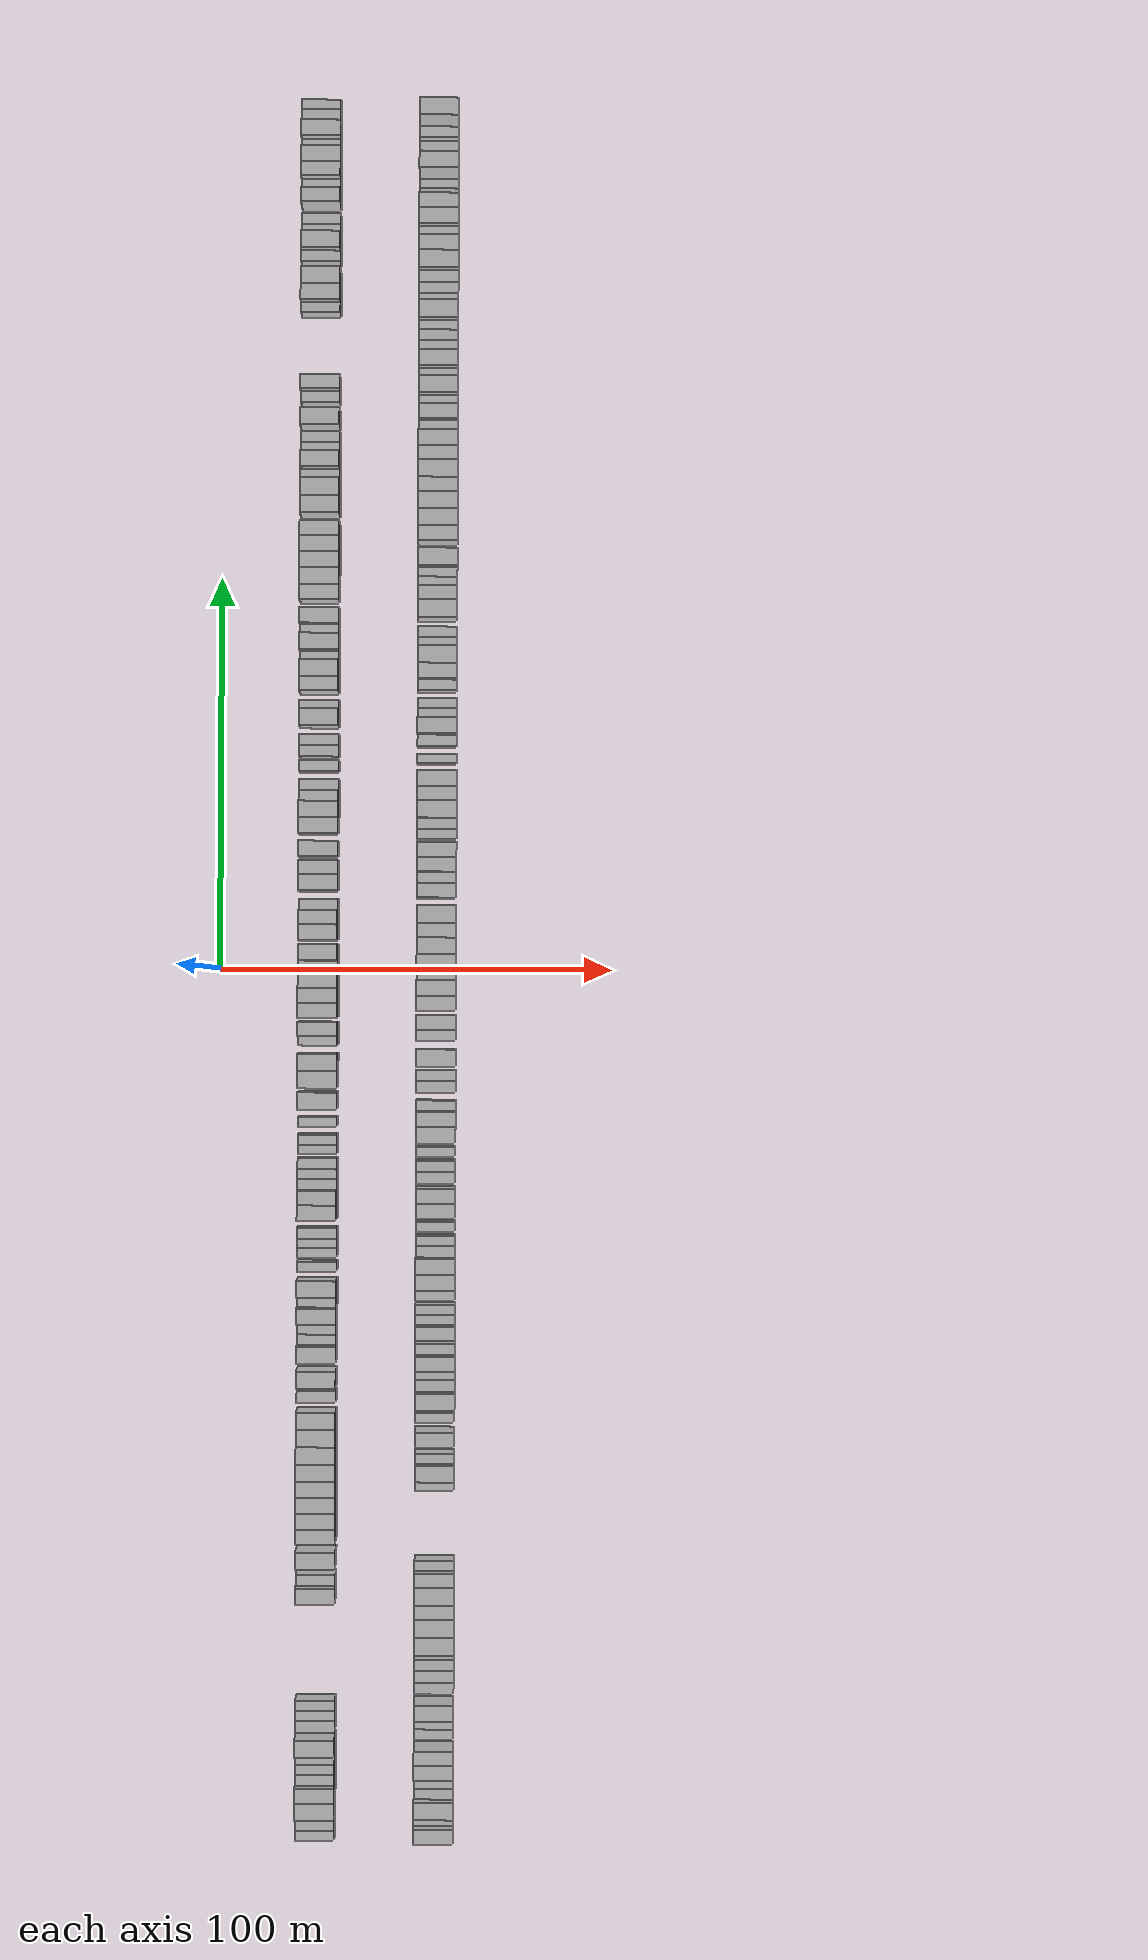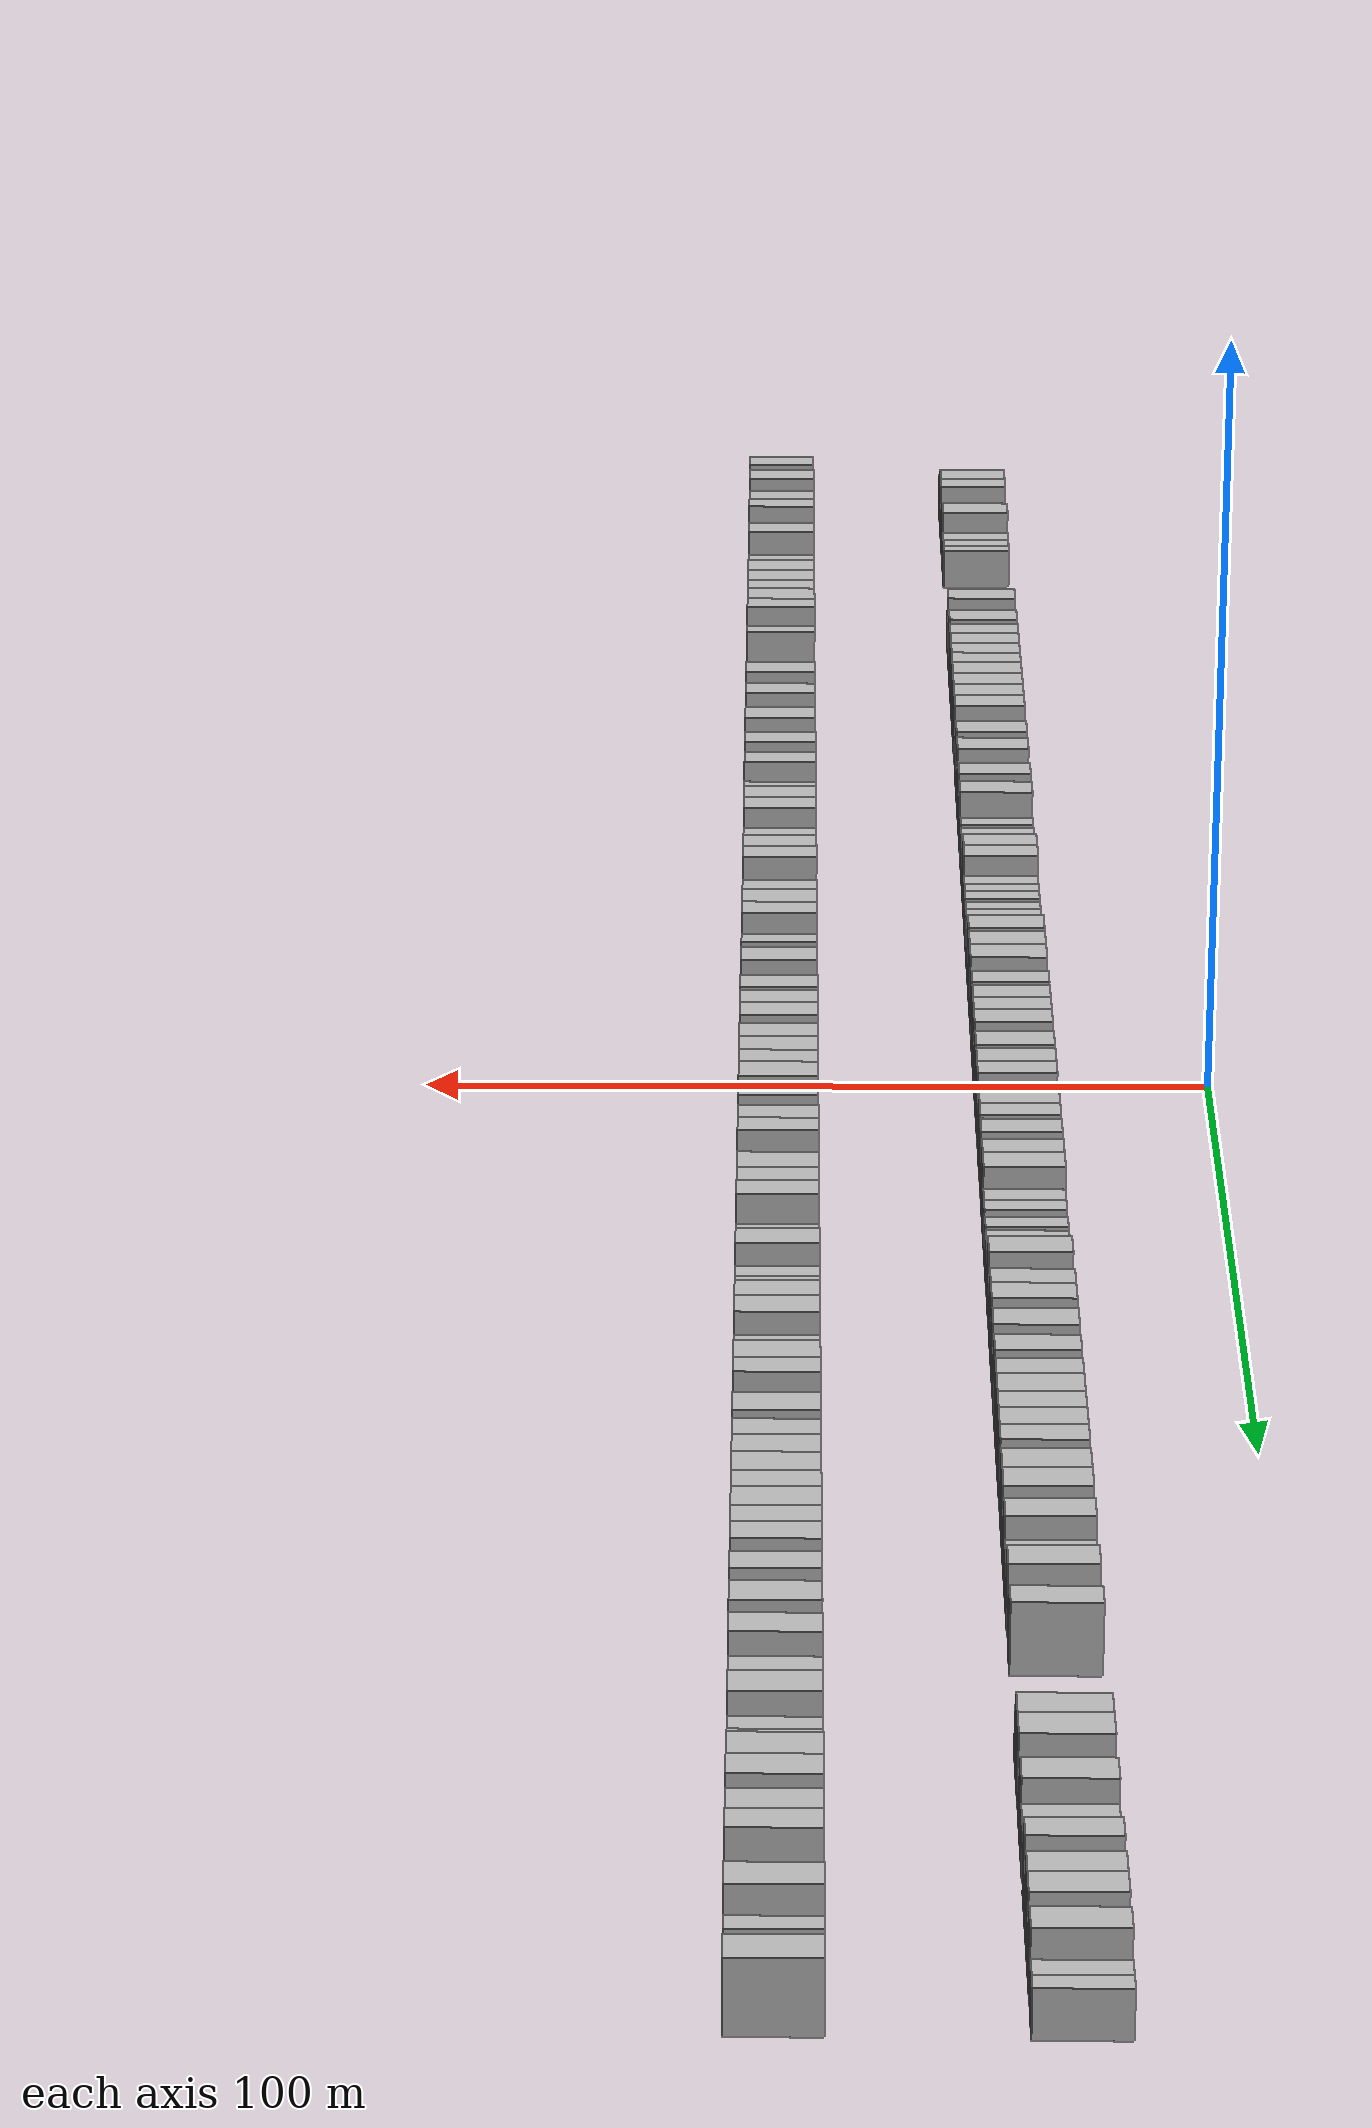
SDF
<sdf version="1.6">
 <world name="default">
  <scene>
   <sky><clouds><speed>12</speed></clouds></sky>
   <ambient>0.4 0.4 0.4 1</ambient>
   <background>0.7 0.7 0.7 1</background>
   <shadows>1</shadows>
  </scene>
  <gravity>0 0 -9.8066</gravity>
  <magnetic_field>6e-06 2.3e-05 -4.2e-05</magnetic_field>
  <physics default="0" name="default_physics" type="ode">
   <ode>
    <solver>
     <type>quick</type>
     <iters>10</iters>
     <sor>1.0</sor>
     <use_dynamic_moi_rescaling>0</use_dynamic_moi_rescaling>
    </solver>
    <constraints>
     <cfm>0</cfm>
     <erp>0.2</erp>
     <contact_max_correcting_vel>100</contact_max_correcting_vel>
     <contact_surface_layer>0.001</contact_surface_layer>
    </constraints>
   </ode>
   <max_step_size>0.004</max_step_size>
   <real_time_factor>1</real_time_factor>
   <real_time_update_rate>250</real_time_update_rate>
  </physics>
  <light name="sun" type="directional">
   <pose>0 0 10 0 0 0</pose>
   <diffuse>0.8 0.8 0.8 1</diffuse>
   <specular>0.2 0.2 0.2 1</specular>
   <attenuation>
    <range>1000</range>
    <constant>0.9</constant>
    <linear>0.01</linear>
    <quadratic>0.001</quadratic>
   </attenuation>
   <direction>-0.5 0.1 -0.9</direction>
  </light>
  <model name="building_1">
   <static>1</static>
   <pose>25.0000 -218.7661 0 0.000000 0.000000 0.000000</pose>
   <link name="link">
    <pose>0 0 3.00 0 0 0</pose>
    <collision name="collision"><geometry><box><size>10.0000 2.4679 6.0000</size></box></geometry></collision>
    <visual name="visual">
     <cast_shadows>0</cast_shadows>
     <geometry><box><size>10.0000 2.4679 6.0000</size></box></geometry>
     <material>
      <script>
       <uri>model://HANNAS_wall/materials/scripts</uri>
       <uri>model://HANNAS_wall/materials/textures</uri>
       <name>vrc/HANNAS_wall</name>
      </script>
     </material>
    </visual>
   </link>
  </model>
  <model name="building_2">
   <static>1</static>
   <pose>25.0000 -216.3126 0 0.000000 0.000000 0.000000</pose>
   <link name="link">
    <pose>0 0 3.00 0 0 0</pose>
    <collision name="collision"><geometry><box><size>10.0000 2.4391 6.0000</size></box></geometry></collision>
    <visual name="visual">
     <cast_shadows>0</cast_shadows>
     <geometry><box><size>10.0000 2.4391 6.0000</size></box></geometry>
     <material>
      <script>
       <uri>model://HANNAS_wall/materials/scripts</uri>
       <uri>model://HANNAS_wall/materials/textures</uri>
       <name>vrc/HANNAS_wall</name>
      </script>
     </material>
    </visual>
   </link>
  </model>
  <model name="building_3">
   <static>1</static>
   <pose>25.0000 -211.9089 0 0.000000 0.000000 0.000000</pose>
   <link name="link">
    <pose>0 0 4.50 0 0 0</pose>
    <collision name="collision"><geometry><box><size>10.0000 4.3683 9.0000</size></box></geometry></collision>
    <visual name="visual">
     <cast_shadows>0</cast_shadows>
     <geometry><box><size>10.0000 4.3683 9.0000</size></box></geometry>
     <material>
      <script>
       <uri>model://HANNAS_wall/materials/scripts</uri>
       <uri>model://HANNAS_wall/materials/textures</uri>
       <name>vrc/HANNAS_wall</name>
      </script>
     </material>
    </visual>
   </link>
  </model>
  <model name="building_4">
   <static>1</static>
   <pose>25.0000 -207.9164 0 0.000000 0.000000 0.000000</pose>
   <link name="link">
    <pose>0 0 4.50 0 0 0</pose>
    <collision name="collision"><geometry><box><size>10.0000 3.6167 9.0000</size></box></geometry></collision>
    <visual name="visual">
     <cast_shadows>0</cast_shadows>
     <geometry><box><size>10.0000 3.6167 9.0000</size></box></geometry>
     <material>
      <script>
       <uri>model://HANNAS_wall/materials/scripts</uri>
       <uri>model://HANNAS_wall/materials/textures</uri>
       <name>vrc/HANNAS_wall</name>
      </script>
     </material>
    </visual>
   </link>
  </model>
  <model name="building_5">
   <static>1</static>
   <pose>25.0000 -204.7812 0 0.000000 0.000000 0.000000</pose>
   <link name="link">
    <pose>0 0 3.00 0 0 0</pose>
    <collision name="collision"><geometry><box><size>10.0000 2.6537 6.0000</size></box></geometry></collision>
    <visual name="visual">
     <cast_shadows>0</cast_shadows>
     <geometry><box><size>10.0000 2.6537 6.0000</size></box></geometry>
     <material>
      <script>
       <uri>model://HANNAS_wall/materials/scripts</uri>
       <uri>model://HANNAS_wall/materials/textures</uri>
       <name>vrc/HANNAS_wall</name>
      </script>
     </material>
    </visual>
   </link>
  </model>
  <model name="building_6">
   <static>1</static>
   <pose>25.0000 -202.2221 0 0.000000 0.000000 0.000000</pose>
   <link name="link">
    <pose>0 0 3.00 0 0 0</pose>
    <collision name="collision"><geometry><box><size>10.0000 2.4645 6.0000</size></box></geometry></collision>
    <visual name="visual">
     <cast_shadows>0</cast_shadows>
     <geometry><box><size>10.0000 2.4645 6.0000</size></box></geometry>
     <material>
      <script>
       <uri>model://HANNAS_wall/materials/scripts</uri>
       <uri>model://HANNAS_wall/materials/textures</uri>
       <name>vrc/HANNAS_wall</name>
      </script>
     </material>
    </visual>
   </link>
  </model>
  <model name="building_7">
   <static>1</static>
   <pose>25.0000 -199.6462 0 0.000000 0.000000 0.000000</pose>
   <link name="link">
    <pose>0 0 3.00 0 0 0</pose>
    <collision name="collision"><geometry><box><size>10.0000 2.6873 6.0000</size></box></geometry></collision>
    <visual name="visual">
     <cast_shadows>0</cast_shadows>
     <geometry><box><size>10.0000 2.6873 6.0000</size></box></geometry>
     <material>
      <script>
       <uri>model://HANNAS_wall/materials/scripts</uri>
       <uri>model://HANNAS_wall/materials/textures</uri>
       <name>vrc/HANNAS_wall</name>
      </script>
     </material>
    </visual>
   </link>
  </model>
  <model name="building_8">
   <static>1</static>
   <pose>25.0000 -196.1025 0 0.000000 0.000000 0.000000</pose>
   <link name="link">
    <pose>0 0 4.50 0 0 0</pose>
    <collision name="collision"><geometry><box><size>10.0000 4.4001 9.0000</size></box></geometry></collision>
    <visual name="visual">
     <cast_shadows>0</cast_shadows>
     <geometry><box><size>10.0000 4.4001 9.0000</size></box></geometry>
     <material>
      <script>
       <uri>model://HANNAS_wall/materials/scripts</uri>
       <uri>model://HANNAS_wall/materials/textures</uri>
       <name>vrc/HANNAS_wall</name>
      </script>
     </material>
    </visual>
   </link>
  </model>
  <model name="building_9">
   <static>1</static>
   <pose>25.0000 -191.4242 0 0.000000 0.000000 0.000000</pose>
   <link name="link">
    <pose>0 0 3.00 0 0 0</pose>
    <collision name="collision"><geometry><box><size>10.0000 2.9565 6.0000</size></box></geometry></collision>
    <visual name="visual">
     <cast_shadows>0</cast_shadows>
     <geometry><box><size>10.0000 2.9565 6.0000</size></box></geometry>
     <material>
      <script>
       <uri>model://HANNAS_wall/materials/scripts</uri>
       <uri>model://HANNAS_wall/materials/textures</uri>
       <name>vrc/HANNAS_wall</name>
      </script>
     </material>
    </visual>
   </link>
  </model>
  <model name="building_10">
   <static>1</static>
   <pose>25.0000 -188.5970 0 0.000000 0.000000 0.000000</pose>
   <link name="link">
    <pose>0 0 3.00 0 0 0</pose>
    <collision name="collision"><geometry><box><size>10.0000 2.6980 6.0000</size></box></geometry></collision>
    <visual name="visual">
     <cast_shadows>0</cast_shadows>
     <geometry><box><size>10.0000 2.6980 6.0000</size></box></geometry>
     <material>
      <script>
       <uri>model://HANNAS_wall/materials/scripts</uri>
       <uri>model://HANNAS_wall/materials/textures</uri>
       <name>vrc/HANNAS_wall</name>
      </script>
     </material>
    </visual>
   </link>
  </model>
  <model name="building_11">
   <static>1</static>
   <pose>25.0000 -186.0118 0 0.000000 0.000000 0.000000</pose>
   <link name="link">
    <pose>0 0 3.00 0 0 0</pose>
    <collision name="collision"><geometry><box><size>10.0000 2.4724 6.0000</size></box></geometry></collision>
    <visual name="visual">
     <cast_shadows>0</cast_shadows>
     <geometry><box><size>10.0000 2.4724 6.0000</size></box></geometry>
     <material>
      <script>
       <uri>model://HANNAS_wall/materials/scripts</uri>
       <uri>model://HANNAS_wall/materials/textures</uri>
       <name>vrc/HANNAS_wall</name>
      </script>
     </material>
    </visual>
   </link>
  </model>
  <model name="building_12">
   <static>1</static>
   <pose>25.0000 -157.7931 0 0.000000 0.000000 0.000000</pose>
   <link name="link">
    <pose>0 0 4.50 0 0 0</pose>
    <collision name="collision"><geometry><box><size>10.0000 3.9883 9.0000</size></box></geometry></collision>
    <visual name="visual">
     <cast_shadows>0</cast_shadows>
     <geometry><box><size>10.0000 3.9883 9.0000</size></box></geometry>
     <material>
      <script>
       <uri>model://HANNAS_wall/materials/scripts</uri>
       <uri>model://HANNAS_wall/materials/textures</uri>
       <name>vrc/HANNAS_wall</name>
      </script>
     </material>
    </visual>
   </link>
  </model>
  <model name="building_13">
   <static>1</static>
   <pose>25.0000 -154.4034 0 0.000000 0.000000 0.000000</pose>
   <link name="link">
    <pose>0 0 3.00 0 0 0</pose>
    <collision name="collision"><geometry><box><size>10.0000 2.7912 6.0000</size></box></geometry></collision>
    <visual name="visual">
     <cast_shadows>0</cast_shadows>
     <geometry><box><size>10.0000 2.7912 6.0000</size></box></geometry>
     <material>
      <script>
       <uri>model://HANNAS_wall/materials/scripts</uri>
       <uri>model://HANNAS_wall/materials/textures</uri>
       <name>vrc/HANNAS_wall</name>
      </script>
     </material>
    </visual>
   </link>
  </model>
  <model name="building_14">
   <static>1</static>
   <pose>25.0000 -148.9291 0 0.000000 0.000000 0.000000</pose>
   <link name="link">
    <pose>0 0 4.50 0 0 0</pose>
    <collision name="collision"><geometry><box><size>10.0000 4.1573 9.0000</size></box></geometry></collision>
    <visual name="visual">
     <cast_shadows>0</cast_shadows>
     <geometry><box><size>10.0000 4.1573 9.0000</size></box></geometry>
     <material>
      <script>
       <uri>model://HANNAS_wall/materials/scripts</uri>
       <uri>model://HANNAS_wall/materials/textures</uri>
       <name>vrc/HANNAS_wall</name>
      </script>
     </material>
    </visual>
   </link>
  </model>
  <model name="building_15">
   <static>1</static>
   <pose>25.0000 -142.9591 0 0.000000 0.000000 0.000000</pose>
   <link name="link">
    <pose>0 0 4.50 0 0 0</pose>
    <collision name="collision"><geometry><box><size>10.0000 3.7828 9.0000</size></box></geometry></collision>
    <visual name="visual">
     <cast_shadows>0</cast_shadows>
     <geometry><box><size>10.0000 3.7828 9.0000</size></box></geometry>
     <material>
      <script>
       <uri>model://HANNAS_wall/materials/scripts</uri>
       <uri>model://HANNAS_wall/materials/textures</uri>
       <name>vrc/HANNAS_wall</name>
      </script>
     </material>
    </visual>
   </link>
  </model>
  <model name="building_16">
   <static>1</static>
   <pose>25.0000 -139.0517 0 0.000000 0.000000 0.000000</pose>
   <link name="link">
    <pose>0 0 4.50 0 0 0</pose>
    <collision name="collision"><geometry><box><size>10.0000 4.0319 9.0000</size></box></geometry></collision>
    <visual name="visual">
     <cast_shadows>0</cast_shadows>
     <geometry><box><size>10.0000 4.0319 9.0000</size></box></geometry>
     <material>
      <script>
       <uri>model://HANNAS_wall/materials/scripts</uri>
       <uri>model://HANNAS_wall/materials/textures</uri>
       <name>vrc/HANNAS_wall</name>
      </script>
     </material>
    </visual>
   </link>
  </model>
  <model name="building_17">
   <static>1</static>
   <pose>25.0000 -135.0709 0 0.000000 0.000000 0.000000</pose>
   <link name="link">
    <pose>0 0 4.50 0 0 0</pose>
    <collision name="collision"><geometry><box><size>10.0000 3.9298 9.0000</size></box></geometry></collision>
    <visual name="visual">
     <cast_shadows>0</cast_shadows>
     <geometry><box><size>10.0000 3.9298 9.0000</size></box></geometry>
     <material>
      <script>
       <uri>model://HANNAS_wall/materials/scripts</uri>
       <uri>model://HANNAS_wall/materials/textures</uri>
       <name>vrc/HANNAS_wall</name>
      </script>
     </material>
    </visual>
   </link>
  </model>
  <model name="building_18">
   <static>1</static>
   <pose>25.0000 -131.0898 0 0.000000 0.000000 0.000000</pose>
   <link name="link">
    <pose>0 0 4.50 0 0 0</pose>
    <collision name="collision"><geometry><box><size>10.0000 4.0324 9.0000</size></box></geometry></collision>
    <visual name="visual">
     <cast_shadows>0</cast_shadows>
     <geometry><box><size>10.0000 4.0324 9.0000</size></box></geometry>
     <material>
      <script>
       <uri>model://HANNAS_wall/materials/scripts</uri>
       <uri>model://HANNAS_wall/materials/textures</uri>
       <name>vrc/HANNAS_wall</name>
      </script>
     </material>
    </visual>
   </link>
  </model>
  <model name="building_19">
   <static>1</static>
   <pose>25.0000 -126.8528 0 0.000000 0.000000 0.000000</pose>
   <link name="link">
    <pose>0 0 4.50 0 0 0</pose>
    <collision name="collision"><geometry><box><size>10.0000 4.4417 9.0000</size></box></geometry></collision>
    <visual name="visual">
     <cast_shadows>0</cast_shadows>
     <geometry><box><size>10.0000 4.4417 9.0000</size></box></geometry>
     <material>
      <script>
       <uri>model://HANNAS_wall/materials/scripts</uri>
       <uri>model://HANNAS_wall/materials/textures</uri>
       <name>vrc/HANNAS_wall</name>
      </script>
     </material>
    </visual>
   </link>
  </model>
  <model name="building_20">
   <static>1</static>
   <pose>25.0000 -122.4812 0 0.000000 0.000000 0.000000</pose>
   <link name="link">
    <pose>0 0 4.50 0 0 0</pose>
    <collision name="collision"><geometry><box><size>10.0000 4.3014 9.0000</size></box></geometry></collision>
    <visual name="visual">
     <cast_shadows>0</cast_shadows>
     <geometry><box><size>10.0000 4.3014 9.0000</size></box></geometry>
     <material>
      <script>
       <uri>model://HANNAS_wall/materials/scripts</uri>
       <uri>model://HANNAS_wall/materials/textures</uri>
       <name>vrc/HANNAS_wall</name>
      </script>
     </material>
    </visual>
   </link>
  </model>
  <model name="building_21">
   <static>1</static>
   <pose>25.0000 -118.1228 0 0.000000 0.000000 0.000000</pose>
   <link name="link">
    <pose>0 0 4.50 0 0 0</pose>
    <collision name="collision"><geometry><box><size>10.0000 4.4153 9.0000</size></box></geometry></collision>
    <visual name="visual">
     <cast_shadows>0</cast_shadows>
     <geometry><box><size>10.0000 4.4153 9.0000</size></box></geometry>
     <material>
      <script>
       <uri>model://HANNAS_wall/materials/scripts</uri>
       <uri>model://HANNAS_wall/materials/textures</uri>
       <name>vrc/HANNAS_wall</name>
      </script>
     </material>
    </visual>
   </link>
  </model>
  <model name="building_22">
   <static>1</static>
   <pose>25.0000 -113.7899 0 0.000000 0.000000 0.000000</pose>
   <link name="link">
    <pose>0 0 4.50 0 0 0</pose>
    <collision name="collision"><geometry><box><size>10.0000 4.2507 9.0000</size></box></geometry></collision>
    <visual name="visual">
     <cast_shadows>0</cast_shadows>
     <geometry><box><size>10.0000 4.2507 9.0000</size></box></geometry>
     <material>
      <script>
       <uri>model://HANNAS_wall/materials/scripts</uri>
       <uri>model://HANNAS_wall/materials/textures</uri>
       <name>vrc/HANNAS_wall</name>
      </script>
     </material>
    </visual>
   </link>
  </model>
  <model name="building_23">
   <static>1</static>
   <pose>25.0000 -108.1817 0 0.000000 0.000000 0.000000</pose>
   <link name="link">
    <pose>0 0 3.00 0 0 0</pose>
    <collision name="collision"><geometry><box><size>10.0000 2.9656 6.0000</size></box></geometry></collision>
    <visual name="visual">
     <cast_shadows>0</cast_shadows>
     <geometry><box><size>10.0000 2.9656 6.0000</size></box></geometry>
     <material>
      <script>
       <uri>model://HANNAS_wall/materials/scripts</uri>
       <uri>model://HANNAS_wall/materials/textures</uri>
       <name>vrc/HANNAS_wall</name>
      </script>
     </material>
    </visual>
   </link>
  </model>
  <model name="building_24">
   <static>1</static>
   <pose>25.0000 -103.4862 0 0.000000 0.000000 0.000000</pose>
   <link name="link">
    <pose>0 0 4.50 0 0 0</pose>
    <collision name="collision"><geometry><box><size>10.0000 4.4254 9.0000</size></box></geometry></collision>
    <visual name="visual">
     <cast_shadows>0</cast_shadows>
     <geometry><box><size>10.0000 4.4254 9.0000</size></box></geometry>
     <material>
      <script>
       <uri>model://HANNAS_wall/materials/scripts</uri>
       <uri>model://HANNAS_wall/materials/textures</uri>
       <name>vrc/HANNAS_wall</name>
      </script>
     </material>
    </visual>
   </link>
  </model>
  <model name="building_25">
   <static>1</static>
   <pose>25.0000 -97.1496 0 0.000000 0.000000 0.000000</pose>
   <link name="link">
    <pose>0 0 4.50 0 0 0</pose>
    <collision name="collision"><geometry><box><size>10.0000 4.2478 9.0000</size></box></geometry></collision>
    <visual name="visual">
     <cast_shadows>0</cast_shadows>
     <geometry><box><size>10.0000 4.2478 9.0000</size></box></geometry>
     <material>
      <script>
       <uri>model://HANNAS_wall/materials/scripts</uri>
       <uri>model://HANNAS_wall/materials/textures</uri>
       <name>vrc/HANNAS_wall</name>
      </script>
     </material>
    </visual>
   </link>
  </model>
  <model name="building_26">
   <static>1</static>
   <pose>25.0000 -93.6836 0 0.000000 0.000000 0.000000</pose>
   <link name="link">
    <pose>0 0 3.00 0 0 0</pose>
    <collision name="collision"><geometry><box><size>10.0000 2.6841 6.0000</size></box></geometry></collision>
    <visual name="visual">
     <cast_shadows>0</cast_shadows>
     <geometry><box><size>10.0000 2.6841 6.0000</size></box></geometry>
     <material>
      <script>
       <uri>model://HANNAS_wall/materials/scripts</uri>
       <uri>model://HANNAS_wall/materials/textures</uri>
       <name>vrc/HANNAS_wall</name>
      </script>
     </material>
    </visual>
   </link>
  </model>
  <model name="building_27">
   <static>1</static>
   <pose>25.0000 -90.9342 0 0.000000 0.000000 0.000000</pose>
   <link name="link">
    <pose>0 0 3.00 0 0 0</pose>
    <collision name="collision"><geometry><box><size>10.0000 2.8148 6.0000</size></box></geometry></collision>
    <visual name="visual">
     <cast_shadows>0</cast_shadows>
     <geometry><box><size>10.0000 2.8148 6.0000</size></box></geometry>
     <material>
      <script>
       <uri>model://HANNAS_wall/materials/scripts</uri>
       <uri>model://HANNAS_wall/materials/textures</uri>
       <name>vrc/HANNAS_wall</name>
      </script>
     </material>
    </visual>
   </link>
  </model>
  <model name="building_28">
   <static>1</static>
   <pose>25.0000 -87.5180 0 0.000000 0.000000 0.000000</pose>
   <link name="link">
    <pose>0 0 4.50 0 0 0</pose>
    <collision name="collision"><geometry><box><size>10.0000 4.0176 9.0000</size></box></geometry></collision>
    <visual name="visual">
     <cast_shadows>0</cast_shadows>
     <geometry><box><size>10.0000 4.0176 9.0000</size></box></geometry>
     <material>
      <script>
       <uri>model://HANNAS_wall/materials/scripts</uri>
       <uri>model://HANNAS_wall/materials/textures</uri>
       <name>vrc/HANNAS_wall</name>
      </script>
     </material>
    </visual>
   </link>
  </model>
  <model name="building_29">
   <static>1</static>
   <pose>25.0000 -84.0877 0 0.000000 0.000000 0.000000</pose>
   <link name="link">
    <pose>0 0 3.00 0 0 0</pose>
    <collision name="collision"><geometry><box><size>10.0000 2.8431 6.0000</size></box></geometry></collision>
    <visual name="visual">
     <cast_shadows>0</cast_shadows>
     <geometry><box><size>10.0000 2.8431 6.0000</size></box></geometry>
     <material>
      <script>
       <uri>model://HANNAS_wall/materials/scripts</uri>
       <uri>model://HANNAS_wall/materials/textures</uri>
       <name>vrc/HANNAS_wall</name>
      </script>
     </material>
    </visual>
   </link>
  </model>
  <model name="building_30">
   <static>1</static>
   <pose>25.0000 -80.6205 0 0.000000 0.000000 0.000000</pose>
   <link name="link">
    <pose>0 0 4.50 0 0 0</pose>
    <collision name="collision"><geometry><box><size>10.0000 4.0912 9.0000</size></box></geometry></collision>
    <visual name="visual">
     <cast_shadows>0</cast_shadows>
     <geometry><box><size>10.0000 4.0912 9.0000</size></box></geometry>
     <material>
      <script>
       <uri>model://HANNAS_wall/materials/scripts</uri>
       <uri>model://HANNAS_wall/materials/textures</uri>
       <name>vrc/HANNAS_wall</name>
      </script>
     </material>
    </visual>
   </link>
  </model>
  <model name="building_31">
   <static>1</static>
   <pose>25.0000 -75.2933 0 0.000000 0.000000 0.000000</pose>
   <link name="link">
    <pose>0 0 3.00 0 0 0</pose>
    <collision name="collision"><geometry><box><size>10.0000 2.5630 6.0000</size></box></geometry></collision>
    <visual name="visual">
     <cast_shadows>0</cast_shadows>
     <geometry><box><size>10.0000 2.5630 6.0000</size></box></geometry>
     <material>
      <script>
       <uri>model://HANNAS_wall/materials/scripts</uri>
       <uri>model://HANNAS_wall/materials/textures</uri>
       <name>vrc/HANNAS_wall</name>
      </script>
     </material>
    </visual>
   </link>
  </model>
  <model name="building_32">
   <static>1</static>
   <pose>25.0000 -71.7716 0 0.000000 0.000000 0.000000</pose>
   <link name="link">
    <pose>0 0 3.00 0 0 0</pose>
    <collision name="collision"><geometry><box><size>10.0000 2.4804 6.0000</size></box></geometry></collision>
    <visual name="visual">
     <cast_shadows>0</cast_shadows>
     <geometry><box><size>10.0000 2.4804 6.0000</size></box></geometry>
     <material>
      <script>
       <uri>model://HANNAS_wall/materials/scripts</uri>
       <uri>model://HANNAS_wall/materials/textures</uri>
       <name>vrc/HANNAS_wall</name>
      </script>
     </material>
    </visual>
   </link>
  </model>
  <model name="building_33">
   <static>1</static>
   <pose>25.0000 -69.3060 0 0.000000 0.000000 0.000000</pose>
   <link name="link">
    <pose>0 0 3.00 0 0 0</pose>
    <collision name="collision"><geometry><box><size>10.0000 2.4508 6.0000</size></box></geometry></collision>
    <visual name="visual">
     <cast_shadows>0</cast_shadows>
     <geometry><box><size>10.0000 2.4508 6.0000</size></box></geometry>
     <material>
      <script>
       <uri>model://HANNAS_wall/materials/scripts</uri>
       <uri>model://HANNAS_wall/materials/textures</uri>
       <name>vrc/HANNAS_wall</name>
      </script>
     </material>
    </visual>
   </link>
  </model>
  <model name="building_34">
   <static>1</static>
   <pose>25.0000 -66.7263 0 0.000000 0.000000 0.000000</pose>
   <link name="link">
    <pose>0 0 3.00 0 0 0</pose>
    <collision name="collision"><geometry><box><size>10.0000 2.7085 6.0000</size></box></geometry></collision>
    <visual name="visual">
     <cast_shadows>0</cast_shadows>
     <geometry><box><size>10.0000 2.7085 6.0000</size></box></geometry>
     <material>
      <script>
       <uri>model://HANNAS_wall/materials/scripts</uri>
       <uri>model://HANNAS_wall/materials/textures</uri>
       <name>vrc/HANNAS_wall</name>
      </script>
     </material>
    </visual>
   </link>
  </model>
  <model name="building_35">
   <static>1</static>
   <pose>25.0000 -61.4168 0 0.000000 0.000000 0.000000</pose>
   <link name="link">
    <pose>0 0 4.50 0 0 0</pose>
    <collision name="collision"><geometry><box><size>10.0000 3.9105 9.0000</size></box></geometry></collision>
    <visual name="visual">
     <cast_shadows>0</cast_shadows>
     <geometry><box><size>10.0000 3.9105 9.0000</size></box></geometry>
     <material>
      <script>
       <uri>model://HANNAS_wall/materials/scripts</uri>
       <uri>model://HANNAS_wall/materials/textures</uri>
       <name>vrc/HANNAS_wall</name>
      </script>
     </material>
    </visual>
   </link>
  </model>
  <model name="building_36">
   <static>1</static>
   <pose>25.0000 -57.6154 0 0.000000 0.000000 0.000000</pose>
   <link name="link">
    <pose>0 0 4.50 0 0 0</pose>
    <collision name="collision"><geometry><box><size>10.0000 3.6923 9.0000</size></box></geometry></collision>
    <visual name="visual">
     <cast_shadows>0</cast_shadows>
     <geometry><box><size>10.0000 3.6923 9.0000</size></box></geometry>
     <material>
      <script>
       <uri>model://HANNAS_wall/materials/scripts</uri>
       <uri>model://HANNAS_wall/materials/textures</uri>
       <name>vrc/HANNAS_wall</name>
      </script>
     </material>
    </visual>
   </link>
  </model>
  <model name="building_37">
   <static>1</static>
   <pose>25.0000 -54.3791 0 0.000000 0.000000 0.000000</pose>
   <link name="link">
    <pose>0 0 3.00 0 0 0</pose>
    <collision name="collision"><geometry><box><size>10.0000 2.7803 6.0000</size></box></geometry></collision>
    <visual name="visual">
     <cast_shadows>0</cast_shadows>
     <geometry><box><size>10.0000 2.7803 6.0000</size></box></geometry>
     <material>
      <script>
       <uri>model://HANNAS_wall/materials/scripts</uri>
       <uri>model://HANNAS_wall/materials/textures</uri>
       <name>vrc/HANNAS_wall</name>
      </script>
     </material>
    </visual>
   </link>
  </model>
  <model name="building_38">
   <static>1</static>
   <pose>25.0000 -51.7858 0 0.000000 0.000000 0.000000</pose>
   <link name="link">
    <pose>0 0 3.00 0 0 0</pose>
    <collision name="collision"><geometry><box><size>10.0000 2.4063 6.0000</size></box></geometry></collision>
    <visual name="visual">
     <cast_shadows>0</cast_shadows>
     <geometry><box><size>10.0000 2.4063 6.0000</size></box></geometry>
     <material>
      <script>
       <uri>model://HANNAS_wall/materials/scripts</uri>
       <uri>model://HANNAS_wall/materials/textures</uri>
       <name>vrc/HANNAS_wall</name>
      </script>
     </material>
    </visual>
   </link>
  </model>
  <model name="building_39">
   <static>1</static>
   <pose>25.0000 -49.1790 0 0.000000 0.000000 0.000000</pose>
   <link name="link">
    <pose>0 0 3.00 0 0 0</pose>
    <collision name="collision"><geometry><box><size>10.0000 2.8073 6.0000</size></box></geometry></collision>
    <visual name="visual">
     <cast_shadows>0</cast_shadows>
     <geometry><box><size>10.0000 2.8073 6.0000</size></box></geometry>
     <material>
      <script>
       <uri>model://HANNAS_wall/materials/scripts</uri>
       <uri>model://HANNAS_wall/materials/textures</uri>
       <name>vrc/HANNAS_wall</name>
      </script>
     </material>
    </visual>
   </link>
  </model>
  <model name="building_40">
   <static>1</static>
   <pose>25.0000 -45.5491 0 0.000000 0.000000 0.000000</pose>
   <link name="link">
    <pose>0 0 3.00 0 0 0</pose>
    <collision name="collision"><geometry><box><size>10.0000 2.4526 6.0000</size></box></geometry></collision>
    <visual name="visual">
     <cast_shadows>0</cast_shadows>
     <geometry><box><size>10.0000 2.4526 6.0000</size></box></geometry>
     <material>
      <script>
       <uri>model://HANNAS_wall/materials/scripts</uri>
       <uri>model://HANNAS_wall/materials/textures</uri>
       <name>vrc/HANNAS_wall</name>
      </script>
     </material>
    </visual>
   </link>
  </model>
  <model name="building_41">
   <static>1</static>
   <pose>25.0000 -43.0538 0 0.000000 0.000000 0.000000</pose>
   <link name="link">
    <pose>0 0 3.00 0 0 0</pose>
    <collision name="collision"><geometry><box><size>10.0000 2.5381 6.0000</size></box></geometry></collision>
    <visual name="visual">
     <cast_shadows>0</cast_shadows>
     <geometry><box><size>10.0000 2.5381 6.0000</size></box></geometry>
     <material>
      <script>
       <uri>model://HANNAS_wall/materials/scripts</uri>
       <uri>model://HANNAS_wall/materials/textures</uri>
       <name>vrc/HANNAS_wall</name>
      </script>
     </material>
    </visual>
   </link>
  </model>
  <model name="building_42">
   <static>1</static>
   <pose>25.0000 -38.5766 0 0.000000 0.000000 0.000000</pose>
   <link name="link">
    <pose>0 0 3.00 0 0 0</pose>
    <collision name="collision"><geometry><box><size>10.0000 2.4163 6.0000</size></box></geometry></collision>
    <visual name="visual">
     <cast_shadows>0</cast_shadows>
     <geometry><box><size>10.0000 2.4163 6.0000</size></box></geometry>
     <material>
      <script>
       <uri>model://HANNAS_wall/materials/scripts</uri>
       <uri>model://HANNAS_wall/materials/textures</uri>
       <name>vrc/HANNAS_wall</name>
      </script>
     </material>
    </visual>
   </link>
  </model>
  <model name="building_43">
   <static>1</static>
   <pose>25.0000 -33.1783 0 0.000000 0.000000 0.000000</pose>
   <link name="link">
    <pose>0 0 4.50 0 0 0</pose>
    <collision name="collision"><geometry><box><size>10.0000 4.3802 9.0000</size></box></geometry></collision>
    <visual name="visual">
     <cast_shadows>0</cast_shadows>
     <geometry><box><size>10.0000 4.3802 9.0000</size></box></geometry>
     <material>
      <script>
       <uri>model://HANNAS_wall/materials/scripts</uri>
       <uri>model://HANNAS_wall/materials/textures</uri>
       <name>vrc/HANNAS_wall</name>
      </script>
     </material>
    </visual>
   </link>
  </model>
  <model name="building_44">
   <static>1</static>
   <pose>25.0000 -27.8201 0 0.000000 0.000000 0.000000</pose>
   <link name="link">
    <pose>0 0 4.50 0 0 0</pose>
    <collision name="collision"><geometry><box><size>10.0000 4.3362 9.0000</size></box></geometry></collision>
    <visual name="visual">
     <cast_shadows>0</cast_shadows>
     <geometry><box><size>10.0000 4.3362 9.0000</size></box></geometry>
     <material>
      <script>
       <uri>model://HANNAS_wall/materials/scripts</uri>
       <uri>model://HANNAS_wall/materials/textures</uri>
       <name>vrc/HANNAS_wall</name>
      </script>
     </material>
    </visual>
   </link>
  </model>
  <model name="building_45">
   <static>1</static>
   <pose>25.0000 -23.4307 0 0.000000 0.000000 0.000000</pose>
   <link name="link">
    <pose>0 0 4.50 0 0 0</pose>
    <collision name="collision"><geometry><box><size>10.0000 4.4427 9.0000</size></box></geometry></collision>
    <visual name="visual">
     <cast_shadows>0</cast_shadows>
     <geometry><box><size>10.0000 4.4427 9.0000</size></box></geometry>
     <material>
      <script>
       <uri>model://HANNAS_wall/materials/scripts</uri>
       <uri>model://HANNAS_wall/materials/textures</uri>
       <name>vrc/HANNAS_wall</name>
      </script>
     </material>
    </visual>
   </link>
  </model>
  <model name="building_46">
   <static>1</static>
   <pose>25.0000 -17.9880 0 0.000000 0.000000 0.000000</pose>
   <link name="link">
    <pose>0 0 3.00 0 0 0</pose>
    <collision name="collision"><geometry><box><size>10.0000 2.4428 6.0000</size></box></geometry></collision>
    <visual name="visual">
     <cast_shadows>0</cast_shadows>
     <geometry><box><size>10.0000 2.4428 6.0000</size></box></geometry>
     <material>
      <script>
       <uri>model://HANNAS_wall/materials/scripts</uri>
       <uri>model://HANNAS_wall/materials/textures</uri>
       <name>vrc/HANNAS_wall</name>
      </script>
     </material>
    </visual>
   </link>
  </model>
  <model name="building_47">
   <static>1</static>
   <pose>25.0000 -14.9655 0 0.000000 0.000000 0.000000</pose>
   <link name="link">
    <pose>0 0 4.50 0 0 0</pose>
    <collision name="collision"><geometry><box><size>10.0000 3.6022 9.0000</size></box></geometry></collision>
    <visual name="visual">
     <cast_shadows>0</cast_shadows>
     <geometry><box><size>10.0000 3.6022 9.0000</size></box></geometry>
     <material>
      <script>
       <uri>model://HANNAS_wall/materials/scripts</uri>
       <uri>model://HANNAS_wall/materials/textures</uri>
       <name>vrc/HANNAS_wall</name>
      </script>
     </material>
    </visual>
   </link>
  </model>
  <model name="building_48">
   <static>1</static>
   <pose>25.0000 -10.2720 0 0.000000 0.000000 0.000000</pose>
   <link name="link">
    <pose>0 0 4.50 0 0 0</pose>
    <collision name="collision"><geometry><box><size>10.0000 3.7848 9.0000</size></box></geometry></collision>
    <visual name="visual">
     <cast_shadows>0</cast_shadows>
     <geometry><box><size>10.0000 3.7848 9.0000</size></box></geometry>
     <material>
      <script>
       <uri>model://HANNAS_wall/materials/scripts</uri>
       <uri>model://HANNAS_wall/materials/textures</uri>
       <name>vrc/HANNAS_wall</name>
      </script>
     </material>
    </visual>
   </link>
  </model>
  <model name="building_49">
   <static>1</static>
   <pose>25.0000 -6.4645 0 0.000000 0.000000 0.000000</pose>
   <link name="link">
    <pose>0 0 4.50 0 0 0</pose>
    <collision name="collision"><geometry><box><size>10.0000 3.8303 9.0000</size></box></geometry></collision>
    <visual name="visual">
     <cast_shadows>0</cast_shadows>
     <geometry><box><size>10.0000 3.8303 9.0000</size></box></geometry>
     <material>
      <script>
       <uri>model://HANNAS_wall/materials/scripts</uri>
       <uri>model://HANNAS_wall/materials/textures</uri>
       <name>vrc/HANNAS_wall</name>
      </script>
     </material>
    </visual>
   </link>
  </model>
  <model name="building_50">
   <static>1</static>
   <pose>25.0000 -2.5199 0 0.000000 0.000000 0.000000</pose>
   <link name="link">
    <pose>0 0 4.50 0 0 0</pose>
    <collision name="collision"><geometry><box><size>10.0000 4.0589 9.0000</size></box></geometry></collision>
    <visual name="visual">
     <cast_shadows>0</cast_shadows>
     <geometry><box><size>10.0000 4.0589 9.0000</size></box></geometry>
     <material>
      <script>
       <uri>model://HANNAS_wall/materials/scripts</uri>
       <uri>model://HANNAS_wall/materials/textures</uri>
       <name>vrc/HANNAS_wall</name>
      </script>
     </material>
    </visual>
   </link>
  </model>
  <model name="building_51">
   <static>1</static>
   <pose>25.0000 0.9249 0 0.000000 0.000000 0.000000</pose>
   <link name="link">
    <pose>0 0 3.00 0 0 0</pose>
    <collision name="collision"><geometry><box><size>10.0000 2.8308 6.0000</size></box></geometry></collision>
    <visual name="visual">
     <cast_shadows>0</cast_shadows>
     <geometry><box><size>10.0000 2.8308 6.0000</size></box></geometry>
     <material>
      <script>
       <uri>model://HANNAS_wall/materials/scripts</uri>
       <uri>model://HANNAS_wall/materials/textures</uri>
       <name>vrc/HANNAS_wall</name>
      </script>
     </material>
    </visual>
   </link>
  </model>
  <model name="building_52">
   <static>1</static>
   <pose>25.0000 4.4178 0 0.000000 0.000000 0.000000</pose>
   <link name="link">
    <pose>0 0 4.50 0 0 0</pose>
    <collision name="collision"><geometry><box><size>10.0000 4.1549 9.0000</size></box></geometry></collision>
    <visual name="visual">
     <cast_shadows>0</cast_shadows>
     <geometry><box><size>10.0000 4.1549 9.0000</size></box></geometry>
     <material>
      <script>
       <uri>model://HANNAS_wall/materials/scripts</uri>
       <uri>model://HANNAS_wall/materials/textures</uri>
       <name>vrc/HANNAS_wall</name>
      </script>
     </material>
    </visual>
   </link>
  </model>
  <model name="building_53">
   <static>1</static>
   <pose>25.0000 9.4551 0 0.000000 0.000000 0.000000</pose>
   <link name="link">
    <pose>0 0 4.50 0 0 0</pose>
    <collision name="collision"><geometry><box><size>10.0000 3.9196 9.0000</size></box></geometry></collision>
    <visual name="visual">
     <cast_shadows>0</cast_shadows>
     <geometry><box><size>10.0000 3.9196 9.0000</size></box></geometry>
     <material>
      <script>
       <uri>model://HANNAS_wall/materials/scripts</uri>
       <uri>model://HANNAS_wall/materials/textures</uri>
       <name>vrc/HANNAS_wall</name>
      </script>
     </material>
    </visual>
   </link>
  </model>
  <model name="building_54">
   <static>1</static>
   <pose>25.0000 13.2608 0 0.000000 0.000000 0.000000</pose>
   <link name="link">
    <pose>0 0 4.50 0 0 0</pose>
    <collision name="collision"><geometry><box><size>10.0000 3.6920 9.0000</size></box></geometry></collision>
    <visual name="visual">
     <cast_shadows>0</cast_shadows>
     <geometry><box><size>10.0000 3.6920 9.0000</size></box></geometry>
     <material>
      <script>
       <uri>model://HANNAS_wall/materials/scripts</uri>
       <uri>model://HANNAS_wall/materials/textures</uri>
       <name>vrc/HANNAS_wall</name>
      </script>
     </material>
    </visual>
   </link>
  </model>
  <model name="building_55">
   <static>1</static>
   <pose>25.0000 16.5639 0 0.000000 0.000000 0.000000</pose>
   <link name="link">
    <pose>0 0 3.00 0 0 0</pose>
    <collision name="collision"><geometry><box><size>10.0000 2.9141 6.0000</size></box></geometry></collision>
    <visual name="visual">
     <cast_shadows>0</cast_shadows>
     <geometry><box><size>10.0000 2.9141 6.0000</size></box></geometry>
     <material>
      <script>
       <uri>model://HANNAS_wall/materials/scripts</uri>
       <uri>model://HANNAS_wall/materials/textures</uri>
       <name>vrc/HANNAS_wall</name>
      </script>
     </material>
    </visual>
   </link>
  </model>
  <model name="building_56">
   <static>1</static>
   <pose>25.0000 22.0654 0 0.000000 0.000000 0.000000</pose>
   <link name="link">
    <pose>0 0 4.50 0 0 0</pose>
    <collision name="collision"><geometry><box><size>10.0000 4.0890 9.0000</size></box></geometry></collision>
    <visual name="visual">
     <cast_shadows>0</cast_shadows>
     <geometry><box><size>10.0000 4.0890 9.0000</size></box></geometry>
     <material>
      <script>
       <uri>model://HANNAS_wall/materials/scripts</uri>
       <uri>model://HANNAS_wall/materials/textures</uri>
       <name>vrc/HANNAS_wall</name>
      </script>
     </material>
    </visual>
   </link>
  </model>
  <model name="building_57">
   <static>1</static>
   <pose>25.0000 25.9217 0 0.000000 0.000000 0.000000</pose>
   <link name="link">
    <pose>0 0 4.50 0 0 0</pose>
    <collision name="collision"><geometry><box><size>10.0000 3.6235 9.0000</size></box></geometry></collision>
    <visual name="visual">
     <cast_shadows>0</cast_shadows>
     <geometry><box><size>10.0000 3.6235 9.0000</size></box></geometry>
     <material>
      <script>
       <uri>model://HANNAS_wall/materials/scripts</uri>
       <uri>model://HANNAS_wall/materials/textures</uri>
       <name>vrc/HANNAS_wall</name>
      </script>
     </material>
    </visual>
   </link>
  </model>
  <model name="building_58">
   <static>1</static>
   <pose>25.0000 30.6726 0 0.000000 0.000000 0.000000</pose>
   <link name="link">
    <pose>0 0 4.50 0 0 0</pose>
    <collision name="collision"><geometry><box><size>10.0000 3.8783 9.0000</size></box></geometry></collision>
    <visual name="visual">
     <cast_shadows>0</cast_shadows>
     <geometry><box><size>10.0000 3.8783 9.0000</size></box></geometry>
     <material>
      <script>
       <uri>model://HANNAS_wall/materials/scripts</uri>
       <uri>model://HANNAS_wall/materials/textures</uri>
       <name>vrc/HANNAS_wall</name>
      </script>
     </material>
    </visual>
   </link>
  </model>
  <model name="building_59">
   <static>1</static>
   <pose>25.0000 36.5301 0 0.000000 0.000000 0.000000</pose>
   <link name="link">
    <pose>0 0 4.50 0 0 0</pose>
    <collision name="collision"><geometry><box><size>10.0000 3.8368 9.0000</size></box></geometry></collision>
    <visual name="visual">
     <cast_shadows>0</cast_shadows>
     <geometry><box><size>10.0000 3.8368 9.0000</size></box></geometry>
     <material>
      <script>
       <uri>model://HANNAS_wall/materials/scripts</uri>
       <uri>model://HANNAS_wall/materials/textures</uri>
       <name>vrc/HANNAS_wall</name>
      </script>
     </material>
    </visual>
   </link>
  </model>
  <model name="building_60">
   <static>1</static>
   <pose>25.0000 40.5798 0 0.000000 0.000000 0.000000</pose>
   <link name="link">
    <pose>0 0 4.50 0 0 0</pose>
    <collision name="collision"><geometry><box><size>10.0000 4.2625 9.0000</size></box></geometry></collision>
    <visual name="visual">
     <cast_shadows>0</cast_shadows>
     <geometry><box><size>10.0000 4.2625 9.0000</size></box></geometry>
     <material>
      <script>
       <uri>model://HANNAS_wall/materials/scripts</uri>
       <uri>model://HANNAS_wall/materials/textures</uri>
       <name>vrc/HANNAS_wall</name>
      </script>
     </material>
    </visual>
   </link>
  </model>
  <model name="building_61">
   <static>1</static>
   <pose>25.0000 44.2027 0 0.000000 0.000000 0.000000</pose>
   <link name="link">
    <pose>0 0 3.00 0 0 0</pose>
    <collision name="collision"><geometry><box><size>10.0000 2.9833 6.0000</size></box></geometry></collision>
    <visual name="visual">
     <cast_shadows>0</cast_shadows>
     <geometry><box><size>10.0000 2.9833 6.0000</size></box></geometry>
     <material>
      <script>
       <uri>model://HANNAS_wall/materials/scripts</uri>
       <uri>model://HANNAS_wall/materials/textures</uri>
       <name>vrc/HANNAS_wall</name>
      </script>
     </material>
    </visual>
   </link>
  </model>
  <model name="building_62">
   <static>1</static>
   <pose>25.0000 47.0833 0 0.000000 0.000000 0.000000</pose>
   <link name="link">
    <pose>0 0 3.00 0 0 0</pose>
    <collision name="collision"><geometry><box><size>10.0000 2.7780 6.0000</size></box></geometry></collision>
    <visual name="visual">
     <cast_shadows>0</cast_shadows>
     <geometry><box><size>10.0000 2.7780 6.0000</size></box></geometry>
     <material>
      <script>
       <uri>model://HANNAS_wall/materials/scripts</uri>
       <uri>model://HANNAS_wall/materials/textures</uri>
       <name>vrc/HANNAS_wall</name>
      </script>
     </material>
    </visual>
   </link>
  </model>
  <model name="building_63">
   <static>1</static>
   <pose>25.0000 51.8106 0 0.000000 0.000000 0.000000</pose>
   <link name="link">
    <pose>0 0 3.00 0 0 0</pose>
    <collision name="collision"><geometry><box><size>10.0000 2.6768 6.0000</size></box></geometry></collision>
    <visual name="visual">
     <cast_shadows>0</cast_shadows>
     <geometry><box><size>10.0000 2.6768 6.0000</size></box></geometry>
     <material>
      <script>
       <uri>model://HANNAS_wall/materials/scripts</uri>
       <uri>model://HANNAS_wall/materials/textures</uri>
       <name>vrc/HANNAS_wall</name>
      </script>
     </material>
    </visual>
   </link>
  </model>
  <model name="building_64">
   <static>1</static>
   <pose>25.0000 55.6346 0 0.000000 0.000000 0.000000</pose>
   <link name="link">
    <pose>0 0 3.00 0 0 0</pose>
    <collision name="collision"><geometry><box><size>10.0000 2.9713 6.0000</size></box></geometry></collision>
    <visual name="visual">
     <cast_shadows>0</cast_shadows>
     <geometry><box><size>10.0000 2.9713 6.0000</size></box></geometry>
     <material>
      <script>
       <uri>model://HANNAS_wall/materials/scripts</uri>
       <uri>model://HANNAS_wall/materials/textures</uri>
       <name>vrc/HANNAS_wall</name>
      </script>
     </material>
    </visual>
   </link>
  </model>
  <model name="building_65">
   <static>1</static>
   <pose>25.0000 58.5050 0 0.000000 0.000000 0.000000</pose>
   <link name="link">
    <pose>0 0 3.00 0 0 0</pose>
    <collision name="collision"><geometry><box><size>10.0000 2.7695 6.0000</size></box></geometry></collision>
    <visual name="visual">
     <cast_shadows>0</cast_shadows>
     <geometry><box><size>10.0000 2.7695 6.0000</size></box></geometry>
     <material>
      <script>
       <uri>model://HANNAS_wall/materials/scripts</uri>
       <uri>model://HANNAS_wall/materials/textures</uri>
       <name>vrc/HANNAS_wall</name>
      </script>
     </material>
    </visual>
   </link>
  </model>
  <model name="building_66">
   <static>1</static>
   <pose>25.0000 64.0120 0 0.000000 0.000000 0.000000</pose>
   <link name="link">
    <pose>0 0 4.50 0 0 0</pose>
    <collision name="collision"><geometry><box><size>10.0000 4.2446 9.0000</size></box></geometry></collision>
    <visual name="visual">
     <cast_shadows>0</cast_shadows>
     <geometry><box><size>10.0000 4.2446 9.0000</size></box></geometry>
     <material>
      <script>
       <uri>model://HANNAS_wall/materials/scripts</uri>
       <uri>model://HANNAS_wall/materials/textures</uri>
       <name>vrc/HANNAS_wall</name>
      </script>
     </material>
    </visual>
   </link>
  </model>
  <model name="building_67">
   <static>1</static>
   <pose>25.0000 67.3540 0 0.000000 0.000000 0.000000</pose>
   <link name="link">
    <pose>0 0 3.00 0 0 0</pose>
    <collision name="collision"><geometry><box><size>10.0000 2.4393 6.0000</size></box></geometry></collision>
    <visual name="visual">
     <cast_shadows>0</cast_shadows>
     <geometry><box><size>10.0000 2.4393 6.0000</size></box></geometry>
     <material>
      <script>
       <uri>model://HANNAS_wall/materials/scripts</uri>
       <uri>model://HANNAS_wall/materials/textures</uri>
       <name>vrc/HANNAS_wall</name>
      </script>
     </material>
    </visual>
   </link>
  </model>
  <model name="building_68">
   <static>1</static>
   <pose>25.0000 72.4273 0 0.000000 0.000000 0.000000</pose>
   <link name="link">
    <pose>0 0 4.50 0 0 0</pose>
    <collision name="collision"><geometry><box><size>10.0000 3.7074 9.0000</size></box></geometry></collision>
    <visual name="visual">
     <cast_shadows>0</cast_shadows>
     <geometry><box><size>10.0000 3.7074 9.0000</size></box></geometry>
     <material>
      <script>
       <uri>model://HANNAS_wall/materials/scripts</uri>
       <uri>model://HANNAS_wall/materials/textures</uri>
       <name>vrc/HANNAS_wall</name>
      </script>
     </material>
    </visual>
   </link>
  </model>
  <model name="building_69">
   <static>1</static>
   <pose>25.0000 76.3592 0 0.000000 0.000000 0.000000</pose>
   <link name="link">
    <pose>0 0 4.50 0 0 0</pose>
    <collision name="collision"><geometry><box><size>10.0000 4.1564 9.0000</size></box></geometry></collision>
    <visual name="visual">
     <cast_shadows>0</cast_shadows>
     <geometry><box><size>10.0000 4.1564 9.0000</size></box></geometry>
     <material>
      <script>
       <uri>model://HANNAS_wall/materials/scripts</uri>
       <uri>model://HANNAS_wall/materials/textures</uri>
       <name>vrc/HANNAS_wall</name>
      </script>
     </material>
    </visual>
   </link>
  </model>
  <model name="building_70">
   <static>1</static>
   <pose>25.0000 79.7335 0 0.000000 0.000000 0.000000</pose>
   <link name="link">
    <pose>0 0 3.00 0 0 0</pose>
    <collision name="collision"><geometry><box><size>10.0000 2.5922 6.0000</size></box></geometry></collision>
    <visual name="visual">
     <cast_shadows>0</cast_shadows>
     <geometry><box><size>10.0000 2.5922 6.0000</size></box></geometry>
     <material>
      <script>
       <uri>model://HANNAS_wall/materials/scripts</uri>
       <uri>model://HANNAS_wall/materials/textures</uri>
       <name>vrc/HANNAS_wall</name>
      </script>
     </material>
    </visual>
   </link>
  </model>
  <model name="building_71">
   <static>1</static>
   <pose>25.0000 83.1222 0 0.000000 0.000000 0.000000</pose>
   <link name="link">
    <pose>0 0 4.50 0 0 0</pose>
    <collision name="collision"><geometry><box><size>10.0000 4.1851 9.0000</size></box></geometry></collision>
    <visual name="visual">
     <cast_shadows>0</cast_shadows>
     <geometry><box><size>10.0000 4.1851 9.0000</size></box></geometry>
     <material>
      <script>
       <uri>model://HANNAS_wall/materials/scripts</uri>
       <uri>model://HANNAS_wall/materials/textures</uri>
       <name>vrc/HANNAS_wall</name>
      </script>
     </material>
    </visual>
   </link>
  </model>
  <model name="building_72">
   <static>1</static>
   <pose>25.0000 86.4798 0 0.000000 0.000000 0.000000</pose>
   <link name="link">
    <pose>0 0 3.00 0 0 0</pose>
    <collision name="collision"><geometry><box><size>10.0000 2.5300 6.0000</size></box></geometry></collision>
    <visual name="visual">
     <cast_shadows>0</cast_shadows>
     <geometry><box><size>10.0000 2.5300 6.0000</size></box></geometry>
     <material>
      <script>
       <uri>model://HANNAS_wall/materials/scripts</uri>
       <uri>model://HANNAS_wall/materials/textures</uri>
       <name>vrc/HANNAS_wall</name>
      </script>
     </material>
    </visual>
   </link>
  </model>
  <model name="building_73">
   <static>1</static>
   <pose>25.0000 89.7529 0 0.000000 0.000000 0.000000</pose>
   <link name="link">
    <pose>0 0 4.50 0 0 0</pose>
    <collision name="collision"><geometry><box><size>10.0000 4.0162 9.0000</size></box></geometry></collision>
    <visual name="visual">
     <cast_shadows>0</cast_shadows>
     <geometry><box><size>10.0000 4.0162 9.0000</size></box></geometry>
     <material>
      <script>
       <uri>model://HANNAS_wall/materials/scripts</uri>
       <uri>model://HANNAS_wall/materials/textures</uri>
       <name>vrc/HANNAS_wall</name>
      </script>
     </material>
    </visual>
   </link>
  </model>
  <model name="building_74">
   <static>1</static>
   <pose>25.0000 95.6042 0 0.000000 0.000000 0.000000</pose>
   <link name="link">
    <pose>0 0 4.50 0 0 0</pose>
    <collision name="collision"><geometry><box><size>10.0000 3.6864 9.0000</size></box></geometry></collision>
    <visual name="visual">
     <cast_shadows>0</cast_shadows>
     <geometry><box><size>10.0000 3.6864 9.0000</size></box></geometry>
     <material>
      <script>
       <uri>model://HANNAS_wall/materials/scripts</uri>
       <uri>model://HANNAS_wall/materials/textures</uri>
       <name>vrc/HANNAS_wall</name>
      </script>
     </material>
    </visual>
   </link>
  </model>
  <model name="building_75">
   <static>1</static>
   <pose>25.0000 99.6594 0 0.000000 0.000000 0.000000</pose>
   <link name="link">
    <pose>0 0 4.50 0 0 0</pose>
    <collision name="collision"><geometry><box><size>10.0000 4.4240 9.0000</size></box></geometry></collision>
    <visual name="visual">
     <cast_shadows>0</cast_shadows>
     <geometry><box><size>10.0000 4.4240 9.0000</size></box></geometry>
     <material>
      <script>
       <uri>model://HANNAS_wall/materials/scripts</uri>
       <uri>model://HANNAS_wall/materials/textures</uri>
       <name>vrc/HANNAS_wall</name>
      </script>
     </material>
    </visual>
   </link>
  </model>
  <model name="building_76">
   <static>1</static>
   <pose>25.0000 103.8612 0 0.000000 0.000000 0.000000</pose>
   <link name="link">
    <pose>0 0 4.50 0 0 0</pose>
    <collision name="collision"><geometry><box><size>10.0000 3.9796 9.0000</size></box></geometry></collision>
    <visual name="visual">
     <cast_shadows>0</cast_shadows>
     <geometry><box><size>10.0000 3.9796 9.0000</size></box></geometry>
     <material>
      <script>
       <uri>model://HANNAS_wall/materials/scripts</uri>
       <uri>model://HANNAS_wall/materials/textures</uri>
       <name>vrc/HANNAS_wall</name>
      </script>
     </material>
    </visual>
   </link>
  </model>
  <model name="building_77">
   <static>1</static>
   <pose>25.0000 107.9376 0 0.000000 0.000000 0.000000</pose>
   <link name="link">
    <pose>0 0 4.50 0 0 0</pose>
    <collision name="collision"><geometry><box><size>10.0000 4.1730 9.0000</size></box></geometry></collision>
    <visual name="visual">
     <cast_shadows>0</cast_shadows>
     <geometry><box><size>10.0000 4.1730 9.0000</size></box></geometry>
     <material>
      <script>
       <uri>model://HANNAS_wall/materials/scripts</uri>
       <uri>model://HANNAS_wall/materials/textures</uri>
       <name>vrc/HANNAS_wall</name>
      </script>
     </material>
    </visual>
   </link>
  </model>
  <model name="building_78">
   <static>1</static>
   <pose>25.0000 111.8554 0 0.000000 0.000000 0.000000</pose>
   <link name="link">
    <pose>0 0 4.50 0 0 0</pose>
    <collision name="collision"><geometry><box><size>10.0000 3.6627 9.0000</size></box></geometry></collision>
    <visual name="visual">
     <cast_shadows>0</cast_shadows>
     <geometry><box><size>10.0000 3.6627 9.0000</size></box></geometry>
     <material>
      <script>
       <uri>model://HANNAS_wall/materials/scripts</uri>
       <uri>model://HANNAS_wall/materials/textures</uri>
       <name>vrc/HANNAS_wall</name>
      </script>
     </material>
    </visual>
   </link>
  </model>
  <model name="building_79">
   <static>1</static>
   <pose>25.0000 117.9090 0 0.000000 0.000000 0.000000</pose>
   <link name="link">
    <pose>0 0 4.50 0 0 0</pose>
    <collision name="collision"><geometry><box><size>10.0000 4.4444 9.0000</size></box></geometry></collision>
    <visual name="visual">
     <cast_shadows>0</cast_shadows>
     <geometry><box><size>10.0000 4.4444 9.0000</size></box></geometry>
     <material>
      <script>
       <uri>model://HANNAS_wall/materials/scripts</uri>
       <uri>model://HANNAS_wall/materials/textures</uri>
       <name>vrc/HANNAS_wall</name>
      </script>
     </material>
    </visual>
   </link>
  </model>
  <model name="building_80">
   <static>1</static>
   <pose>25.0000 122.3811 0 0.000000 0.000000 0.000000</pose>
   <link name="link">
    <pose>0 0 4.50 0 0 0</pose>
    <collision name="collision"><geometry><box><size>10.0000 4.4999 9.0000</size></box></geometry></collision>
    <visual name="visual">
     <cast_shadows>0</cast_shadows>
     <geometry><box><size>10.0000 4.4999 9.0000</size></box></geometry>
     <material>
      <script>
       <uri>model://HANNAS_wall/materials/scripts</uri>
       <uri>model://HANNAS_wall/materials/textures</uri>
       <name>vrc/HANNAS_wall</name>
      </script>
     </material>
    </visual>
   </link>
  </model>
  <model name="building_81">
   <static>1</static>
   <pose>25.0000 126.0131 0 0.000000 0.000000 0.000000</pose>
   <link name="link">
    <pose>0 0 3.00 0 0 0</pose>
    <collision name="collision"><geometry><box><size>10.0000 2.7641 6.0000</size></box></geometry></collision>
    <visual name="visual">
     <cast_shadows>0</cast_shadows>
     <geometry><box><size>10.0000 2.7641 6.0000</size></box></geometry>
     <material>
      <script>
       <uri>model://HANNAS_wall/materials/scripts</uri>
       <uri>model://HANNAS_wall/materials/textures</uri>
       <name>vrc/HANNAS_wall</name>
      </script>
     </material>
    </visual>
   </link>
  </model>
  <model name="building_82">
   <static>1</static>
   <pose>25.0000 129.4525 0 0.000000 0.000000 0.000000</pose>
   <link name="link">
    <pose>0 0 4.50 0 0 0</pose>
    <collision name="collision"><geometry><box><size>10.0000 4.1146 9.0000</size></box></geometry></collision>
    <visual name="visual">
     <cast_shadows>0</cast_shadows>
     <geometry><box><size>10.0000 4.1146 9.0000</size></box></geometry>
     <material>
      <script>
       <uri>model://HANNAS_wall/materials/scripts</uri>
       <uri>model://HANNAS_wall/materials/textures</uri>
       <name>vrc/HANNAS_wall</name>
      </script>
     </material>
    </visual>
   </link>
  </model>
  <model name="building_83">
   <static>1</static>
   <pose>25.0000 132.8414 0 0.000000 0.000000 0.000000</pose>
   <link name="link">
    <pose>0 0 3.00 0 0 0</pose>
    <collision name="collision"><geometry><box><size>10.0000 2.6632 6.0000</size></box></geometry></collision>
    <visual name="visual">
     <cast_shadows>0</cast_shadows>
     <geometry><box><size>10.0000 2.6632 6.0000</size></box></geometry>
     <material>
      <script>
       <uri>model://HANNAS_wall/materials/scripts</uri>
       <uri>model://HANNAS_wall/materials/textures</uri>
       <name>vrc/HANNAS_wall</name>
      </script>
     </material>
    </visual>
   </link>
  </model>
  <model name="building_84">
   <static>1</static>
   <pose>25.0000 135.6167 0 0.000000 0.000000 0.000000</pose>
   <link name="link">
    <pose>0 0 3.00 0 0 0</pose>
    <collision name="collision"><geometry><box><size>10.0000 2.8875 6.0000</size></box></geometry></collision>
    <visual name="visual">
     <cast_shadows>0</cast_shadows>
     <geometry><box><size>10.0000 2.8875 6.0000</size></box></geometry>
     <material>
      <script>
       <uri>model://HANNAS_wall/materials/scripts</uri>
       <uri>model://HANNAS_wall/materials/textures</uri>
       <name>vrc/HANNAS_wall</name>
      </script>
     </material>
    </visual>
   </link>
  </model>
  <model name="building_85">
   <static>1</static>
   <pose>25.0000 140.2518 0 0.000000 0.000000 0.000000</pose>
   <link name="link">
    <pose>0 0 4.50 0 0 0</pose>
    <collision name="collision"><geometry><box><size>10.0000 4.3826 9.0000</size></box></geometry></collision>
    <visual name="visual">
     <cast_shadows>0</cast_shadows>
     <geometry><box><size>10.0000 4.3826 9.0000</size></box></geometry>
     <material>
      <script>
       <uri>model://HANNAS_wall/materials/scripts</uri>
       <uri>model://HANNAS_wall/materials/textures</uri>
       <name>vrc/HANNAS_wall</name>
      </script>
     </material>
    </visual>
   </link>
  </model>
  <model name="building_86">
   <static>1</static>
   <pose>25.0000 145.7837 0 0.000000 0.000000 0.000000</pose>
   <link name="link">
    <pose>0 0 3.00 0 0 0</pose>
    <collision name="collision"><geometry><box><size>10.0000 2.6813 6.0000</size></box></geometry></collision>
    <visual name="visual">
     <cast_shadows>0</cast_shadows>
     <geometry><box><size>10.0000 2.6813 6.0000</size></box></geometry>
     <material>
      <script>
       <uri>model://HANNAS_wall/materials/scripts</uri>
       <uri>model://HANNAS_wall/materials/textures</uri>
       <name>vrc/HANNAS_wall</name>
      </script>
     </material>
    </visual>
   </link>
  </model>
  <model name="building_87">
   <static>1</static>
   <pose>25.0000 148.9805 0 0.000000 0.000000 0.000000</pose>
   <link name="link">
    <pose>0 0 4.50 0 0 0</pose>
    <collision name="collision"><geometry><box><size>10.0000 3.7122 9.0000</size></box></geometry></collision>
    <visual name="visual">
     <cast_shadows>0</cast_shadows>
     <geometry><box><size>10.0000 3.7122 9.0000</size></box></geometry>
     <material>
      <script>
       <uri>model://HANNAS_wall/materials/scripts</uri>
       <uri>model://HANNAS_wall/materials/textures</uri>
       <name>vrc/HANNAS_wall</name>
      </script>
     </material>
    </visual>
   </link>
  </model>
  <model name="building_88">
   <static>1</static>
   <pose>25.0000 168.6250 0 0.000000 0.000000 0.000000</pose>
   <link name="link">
    <pose>0 0 3.00 0 0 0</pose>
    <collision name="collision"><geometry><box><size>10.0000 2.5256 6.0000</size></box></geometry></collision>
    <visual name="visual">
     <cast_shadows>0</cast_shadows>
     <geometry><box><size>10.0000 2.5256 6.0000</size></box></geometry>
     <material>
      <script>
       <uri>model://HANNAS_wall/materials/scripts</uri>
       <uri>model://HANNAS_wall/materials/textures</uri>
       <name>vrc/HANNAS_wall</name>
      </script>
     </material>
    </visual>
   </link>
  </model>
  <model name="building_89">
   <static>1</static>
   <pose>25.0000 171.9140 0 0.000000 0.000000 0.000000</pose>
   <link name="link">
    <pose>0 0 4.50 0 0 0</pose>
    <collision name="collision"><geometry><box><size>10.0000 4.0523 9.0000</size></box></geometry></collision>
    <visual name="visual">
     <cast_shadows>0</cast_shadows>
     <geometry><box><size>10.0000 4.0523 9.0000</size></box></geometry>
     <material>
      <script>
       <uri>model://HANNAS_wall/materials/scripts</uri>
       <uri>model://HANNAS_wall/materials/textures</uri>
       <name>vrc/HANNAS_wall</name>
      </script>
     </material>
    </visual>
   </link>
  </model>
  <model name="building_90">
   <static>1</static>
   <pose>25.0000 176.1013 0 0.000000 0.000000 0.000000</pose>
   <link name="link">
    <pose>0 0 4.50 0 0 0</pose>
    <collision name="collision"><geometry><box><size>10.0000 4.3224 9.0000</size></box></geometry></collision>
    <visual name="visual">
     <cast_shadows>0</cast_shadows>
     <geometry><box><size>10.0000 4.3224 9.0000</size></box></geometry>
     <material>
      <script>
       <uri>model://HANNAS_wall/materials/scripts</uri>
       <uri>model://HANNAS_wall/materials/textures</uri>
       <name>vrc/HANNAS_wall</name>
      </script>
     </material>
    </visual>
   </link>
  </model>
  <model name="building_91">
   <static>1</static>
   <pose>25.0000 181.6408 0 0.000000 0.000000 0.000000</pose>
   <link name="link">
    <pose>0 0 3.00 0 0 0</pose>
    <collision name="collision"><geometry><box><size>10.0000 2.7566 6.0000</size></box></geometry></collision>
    <visual name="visual">
     <cast_shadows>0</cast_shadows>
     <geometry><box><size>10.0000 2.7566 6.0000</size></box></geometry>
     <material>
      <script>
       <uri>model://HANNAS_wall/materials/scripts</uri>
       <uri>model://HANNAS_wall/materials/textures</uri>
       <name>vrc/HANNAS_wall</name>
      </script>
     </material>
    </visual>
   </link>
  </model>
  <model name="building_92">
   <static>1</static>
   <pose>25.0000 185.1076 0 0.000000 0.000000 0.000000</pose>
   <link name="link">
    <pose>0 0 4.50 0 0 0</pose>
    <collision name="collision"><geometry><box><size>10.0000 4.1772 9.0000</size></box></geometry></collision>
    <visual name="visual">
     <cast_shadows>0</cast_shadows>
     <geometry><box><size>10.0000 4.1772 9.0000</size></box></geometry>
     <material>
      <script>
       <uri>model://HANNAS_wall/materials/scripts</uri>
       <uri>model://HANNAS_wall/materials/textures</uri>
       <name>vrc/HANNAS_wall</name>
      </script>
     </material>
    </visual>
   </link>
  </model>
  <model name="building_93">
   <static>1</static>
   <pose>25.0000 188.5227 0 0.000000 0.000000 0.000000</pose>
   <link name="link">
    <pose>0 0 3.00 0 0 0</pose>
    <collision name="collision"><geometry><box><size>10.0000 2.6529 6.0000</size></box></geometry></collision>
    <visual name="visual">
     <cast_shadows>0</cast_shadows>
     <geometry><box><size>10.0000 2.6529 6.0000</size></box></geometry>
     <material>
      <script>
       <uri>model://HANNAS_wall/materials/scripts</uri>
       <uri>model://HANNAS_wall/materials/textures</uri>
       <name>vrc/HANNAS_wall</name>
      </script>
     </material>
    </visual>
   </link>
  </model>
  <model name="building_94">
   <static>1</static>
   <pose>25.0000 191.2534 0 0.000000 0.000000 0.000000</pose>
   <link name="link">
    <pose>0 0 3.00 0 0 0</pose>
    <collision name="collision"><geometry><box><size>10.0000 2.8085 6.0000</size></box></geometry></collision>
    <visual name="visual">
     <cast_shadows>0</cast_shadows>
     <geometry><box><size>10.0000 2.8085 6.0000</size></box></geometry>
     <material>
      <script>
       <uri>model://HANNAS_wall/materials/scripts</uri>
       <uri>model://HANNAS_wall/materials/textures</uri>
       <name>vrc/HANNAS_wall</name>
      </script>
     </material>
    </visual>
   </link>
  </model>
  <model name="building_95">
   <static>1</static>
   <pose>25.0000 196.4663 0 0.000000 0.000000 0.000000</pose>
   <link name="link">
    <pose>0 0 4.50 0 0 0</pose>
    <collision name="collision"><geometry><box><size>10.0000 3.6174 9.0000</size></box></geometry></collision>
    <visual name="visual">
     <cast_shadows>0</cast_shadows>
     <geometry><box><size>10.0000 3.6174 9.0000</size></box></geometry>
     <material>
      <script>
       <uri>model://HANNAS_wall/materials/scripts</uri>
       <uri>model://HANNAS_wall/materials/textures</uri>
       <name>vrc/HANNAS_wall</name>
      </script>
     </material>
    </visual>
   </link>
  </model>
  <model name="building_96">
   <static>1</static>
   <pose>25.0000 199.7442 0 0.000000 0.000000 0.000000</pose>
   <link name="link">
    <pose>0 0 3.00 0 0 0</pose>
    <collision name="collision"><geometry><box><size>10.0000 2.9382 6.0000</size></box></geometry></collision>
    <visual name="visual">
     <cast_shadows>0</cast_shadows>
     <geometry><box><size>10.0000 2.9382 6.0000</size></box></geometry>
     <material>
      <script>
       <uri>model://HANNAS_wall/materials/scripts</uri>
       <uri>model://HANNAS_wall/materials/textures</uri>
       <name>vrc/HANNAS_wall</name>
      </script>
     </material>
    </visual>
   </link>
  </model>
  <model name="building_97">
   <static>1</static>
   <pose>25.0000 203.0771 0 0.000000 0.000000 0.000000</pose>
   <link name="link">
    <pose>0 0 4.50 0 0 0</pose>
    <collision name="collision"><geometry><box><size>10.0000 3.7277 9.0000</size></box></geometry></collision>
    <visual name="visual">
     <cast_shadows>0</cast_shadows>
     <geometry><box><size>10.0000 3.7277 9.0000</size></box></geometry>
     <material>
      <script>
       <uri>model://HANNAS_wall/materials/scripts</uri>
       <uri>model://HANNAS_wall/materials/textures</uri>
       <name>vrc/HANNAS_wall</name>
      </script>
     </material>
    </visual>
   </link>
  </model>
  <model name="building_98">
   <static>1</static>
   <pose>25.0000 206.9092 0 0.000000 0.000000 0.000000</pose>
   <link name="link">
    <pose>0 0 4.50 0 0 0</pose>
    <collision name="collision"><geometry><box><size>10.0000 3.9366 9.0000</size></box></geometry></collision>
    <visual name="visual">
     <cast_shadows>0</cast_shadows>
     <geometry><box><size>10.0000 3.9366 9.0000</size></box></geometry>
     <material>
      <script>
       <uri>model://HANNAS_wall/materials/scripts</uri>
       <uri>model://HANNAS_wall/materials/textures</uri>
       <name>vrc/HANNAS_wall</name>
      </script>
     </material>
    </visual>
   </link>
  </model>
  <model name="building_99">
   <static>1</static>
   <pose>25.0000 210.2032 0 0.000000 0.000000 0.000000</pose>
   <link name="link">
    <pose>0 0 3.00 0 0 0</pose>
    <collision name="collision"><geometry><box><size>10.0000 2.6513 6.0000</size></box></geometry></collision>
    <visual name="visual">
     <cast_shadows>0</cast_shadows>
     <geometry><box><size>10.0000 2.6513 6.0000</size></box></geometry>
     <material>
      <script>
       <uri>model://HANNAS_wall/materials/scripts</uri>
       <uri>model://HANNAS_wall/materials/textures</uri>
       <name>vrc/HANNAS_wall</name>
      </script>
     </material>
    </visual>
   </link>
  </model>
  <model name="building_100">
   <static>1</static>
   <pose>25.0000 213.4750 0 0.000000 0.000000 0.000000</pose>
   <link name="link">
    <pose>0 0 4.50 0 0 0</pose>
    <collision name="collision"><geometry><box><size>10.0000 3.8925 9.0000</size></box></geometry></collision>
    <visual name="visual">
     <cast_shadows>0</cast_shadows>
     <geometry><box><size>10.0000 3.8925 9.0000</size></box></geometry>
     <material>
      <script>
       <uri>model://HANNAS_wall/materials/scripts</uri>
       <uri>model://HANNAS_wall/materials/textures</uri>
       <name>vrc/HANNAS_wall</name>
      </script>
     </material>
    </visual>
   </link>
  </model>
  <model name="building_101">
   <static>1</static>
   <pose>25.0000 217.7741 0 0.000000 0.000000 0.000000</pose>
   <link name="link">
    <pose>0 0 3.00 0 0 0</pose>
    <collision name="collision"><geometry><box><size>10.0000 2.7057 6.0000</size></box></geometry></collision>
    <visual name="visual">
     <cast_shadows>0</cast_shadows>
     <geometry><box><size>10.0000 2.7057 6.0000</size></box></geometry>
     <material>
      <script>
       <uri>model://HANNAS_wall/materials/scripts</uri>
       <uri>model://HANNAS_wall/materials/textures</uri>
       <name>vrc/HANNAS_wall</name>
      </script>
     </material>
    </visual>
   </link>
  </model>
  <model name="building_102">
   <static>1</static>
   <pose>25.0000 220.3564 0 0.000000 0.000000 0.000000</pose>
   <link name="link">
    <pose>0 0 3.00 0 0 0</pose>
    <collision name="collision"><geometry><box><size>10.0000 2.4588 6.0000</size></box></geometry></collision>
    <visual name="visual">
     <cast_shadows>0</cast_shadows>
     <geometry><box><size>10.0000 2.4588 6.0000</size></box></geometry>
     <material>
      <script>
       <uri>model://HANNAS_wall/materials/scripts</uri>
       <uri>model://HANNAS_wall/materials/textures</uri>
       <name>vrc/HANNAS_wall</name>
      </script>
     </material>
    </visual>
   </link>
  </model>
  <model name="building_103">
   <static>1</static>
   <pose>55.0000 -218.1154 0 0.000000 0.000000 0.000000</pose>
   <link name="link">
    <pose>0 0 4.50 0 0 0</pose>
    <collision name="collision"><geometry><box><size>10.0000 3.7692 9.0000</size></box></geometry></collision>
    <visual name="visual">
     <cast_shadows>0</cast_shadows>
     <geometry><box><size>10.0000 3.7692 9.0000</size></box></geometry>
     <material>
      <script>
       <uri>model://HANNAS_wall/materials/scripts</uri>
       <uri>model://HANNAS_wall/materials/textures</uri>
       <name>vrc/HANNAS_wall</name>
      </script>
     </material>
    </visual>
   </link>
  </model>
  <model name="building_104">
   <static>1</static>
   <pose>55.0000 -215.0028 0 0.000000 0.000000 0.000000</pose>
   <link name="link">
    <pose>0 0 3.00 0 0 0</pose>
    <collision name="collision"><geometry><box><size>10.0000 2.4561 6.0000</size></box></geometry></collision>
    <visual name="visual">
     <cast_shadows>0</cast_shadows>
     <geometry><box><size>10.0000 2.4561 6.0000</size></box></geometry>
     <material>
      <script>
       <uri>model://HANNAS_wall/materials/scripts</uri>
       <uri>model://HANNAS_wall/materials/textures</uri>
       <name>vrc/HANNAS_wall</name>
      </script>
     </material>
    </visual>
   </link>
  </model>
  <model name="building_105">
   <static>1</static>
   <pose>55.0000 -211.6357 0 0.000000 0.000000 0.000000</pose>
   <link name="link">
    <pose>0 0 4.50 0 0 0</pose>
    <collision name="collision"><geometry><box><size>10.0000 4.2781 9.0000</size></box></geometry></collision>
    <visual name="visual">
     <cast_shadows>0</cast_shadows>
     <geometry><box><size>10.0000 4.2781 9.0000</size></box></geometry>
     <material>
      <script>
       <uri>model://HANNAS_wall/materials/scripts</uri>
       <uri>model://HANNAS_wall/materials/textures</uri>
       <name>vrc/HANNAS_wall</name>
      </script>
     </material>
    </visual>
   </link>
  </model>
  <model name="building_106">
   <static>1</static>
   <pose>55.0000 -208.1292 0 0.000000 0.000000 0.000000</pose>
   <link name="link">
    <pose>0 0 3.00 0 0 0</pose>
    <collision name="collision"><geometry><box><size>10.0000 2.7350 6.0000</size></box></geometry></collision>
    <visual name="visual">
     <cast_shadows>0</cast_shadows>
     <geometry><box><size>10.0000 2.7350 6.0000</size></box></geometry>
     <material>
      <script>
       <uri>model://HANNAS_wall/materials/scripts</uri>
       <uri>model://HANNAS_wall/materials/textures</uri>
       <name>vrc/HANNAS_wall</name>
      </script>
     </material>
    </visual>
   </link>
  </model>
  <model name="building_107">
   <static>1</static>
   <pose>55.0000 -205.3541 0 0.000000 0.000000 0.000000</pose>
   <link name="link">
    <pose>0 0 3.00 0 0 0</pose>
    <collision name="collision"><geometry><box><size>10.0000 2.8151 6.0000</size></box></geometry></collision>
    <visual name="visual">
     <cast_shadows>0</cast_shadows>
     <geometry><box><size>10.0000 2.8151 6.0000</size></box></geometry>
     <material>
      <script>
       <uri>model://HANNAS_wall/materials/scripts</uri>
       <uri>model://HANNAS_wall/materials/textures</uri>
       <name>vrc/HANNAS_wall</name>
      </script>
     </material>
    </visual>
   </link>
  </model>
  <model name="building_108">
   <static>1</static>
   <pose>55.0000 -202.0923 0 0.000000 0.000000 0.000000</pose>
   <link name="link">
    <pose>0 0 4.50 0 0 0</pose>
    <collision name="collision"><geometry><box><size>10.0000 3.7086 9.0000</size></box></geometry></collision>
    <visual name="visual">
     <cast_shadows>0</cast_shadows>
     <geometry><box><size>10.0000 3.7086 9.0000</size></box></geometry>
     <material>
      <script>
       <uri>model://HANNAS_wall/materials/scripts</uri>
       <uri>model://HANNAS_wall/materials/textures</uri>
       <name>vrc/HANNAS_wall</name>
      </script>
     </material>
    </visual>
   </link>
  </model>
  <model name="building_109">
   <static>1</static>
   <pose>55.0000 -198.4303 0 0.000000 0.000000 0.000000</pose>
   <link name="link">
    <pose>0 0 4.50 0 0 0</pose>
    <collision name="collision"><geometry><box><size>10.0000 3.6152 9.0000</size></box></geometry></collision>
    <visual name="visual">
     <cast_shadows>0</cast_shadows>
     <geometry><box><size>10.0000 3.6152 9.0000</size></box></geometry>
     <material>
      <script>
       <uri>model://HANNAS_wall/materials/scripts</uri>
       <uri>model://HANNAS_wall/materials/textures</uri>
       <name>vrc/HANNAS_wall</name>
      </script>
     </material>
    </visual>
   </link>
  </model>
  <model name="building_110">
   <static>1</static>
   <pose>55.0000 -193.2518 0 0.000000 0.000000 0.000000</pose>
   <link name="link">
    <pose>0 0 3.00 0 0 0</pose>
    <collision name="collision"><geometry><box><size>10.0000 2.7418 6.0000</size></box></geometry></collision>
    <visual name="visual">
     <cast_shadows>0</cast_shadows>
     <geometry><box><size>10.0000 2.7418 6.0000</size></box></geometry>
     <material>
      <script>
       <uri>model://HANNAS_wall/materials/scripts</uri>
       <uri>model://HANNAS_wall/materials/textures</uri>
       <name>vrc/HANNAS_wall</name>
      </script>
     </material>
    </visual>
   </link>
  </model>
  <model name="building_111">
   <static>1</static>
   <pose>55.0000 -190.4499 0 0.000000 0.000000 0.000000</pose>
   <link name="link">
    <pose>0 0 3.00 0 0 0</pose>
    <collision name="collision"><geometry><box><size>10.0000 2.8620 6.0000</size></box></geometry></collision>
    <visual name="visual">
     <cast_shadows>0</cast_shadows>
     <geometry><box><size>10.0000 2.8620 6.0000</size></box></geometry>
     <material>
      <script>
       <uri>model://HANNAS_wall/materials/scripts</uri>
       <uri>model://HANNAS_wall/materials/textures</uri>
       <name>vrc/HANNAS_wall</name>
      </script>
     </material>
    </visual>
   </link>
  </model>
  <model name="building_112">
   <static>1</static>
   <pose>55.0000 -187.0399 0 0.000000 0.000000 0.000000</pose>
   <link name="link">
    <pose>0 0 4.50 0 0 0</pose>
    <collision name="collision"><geometry><box><size>10.0000 3.9580 9.0000</size></box></geometry></collision>
    <visual name="visual">
     <cast_shadows>0</cast_shadows>
     <geometry><box><size>10.0000 3.9580 9.0000</size></box></geometry>
     <material>
      <script>
       <uri>model://HANNAS_wall/materials/scripts</uri>
       <uri>model://HANNAS_wall/materials/textures</uri>
       <name>vrc/HANNAS_wall</name>
      </script>
     </material>
    </visual>
   </link>
  </model>
  <model name="building_113">
   <static>1</static>
   <pose>55.0000 -181.6062 0 0.000000 0.000000 0.000000</pose>
   <link name="link">
    <pose>0 0 3.00 0 0 0</pose>
    <collision name="collision"><geometry><box><size>10.0000 2.9096 6.0000</size></box></geometry></collision>
    <visual name="visual">
     <cast_shadows>0</cast_shadows>
     <geometry><box><size>10.0000 2.9096 6.0000</size></box></geometry>
     <material>
      <script>
       <uri>model://HANNAS_wall/materials/scripts</uri>
       <uri>model://HANNAS_wall/materials/textures</uri>
       <name>vrc/HANNAS_wall</name>
      </script>
     </material>
    </visual>
   </link>
  </model>
  <model name="building_114">
   <static>1</static>
   <pose>55.0000 -178.6885 0 0.000000 0.000000 0.000000</pose>
   <link name="link">
    <pose>0 0 3.00 0 0 0</pose>
    <collision name="collision"><geometry><box><size>10.0000 2.9256 6.0000</size></box></geometry></collision>
    <visual name="visual">
     <cast_shadows>0</cast_shadows>
     <geometry><box><size>10.0000 2.9256 6.0000</size></box></geometry>
     <material>
      <script>
       <uri>model://HANNAS_wall/materials/scripts</uri>
       <uri>model://HANNAS_wall/materials/textures</uri>
       <name>vrc/HANNAS_wall</name>
      </script>
     </material>
    </visual>
   </link>
  </model>
  <model name="building_115">
   <static>1</static>
   <pose>55.0000 -175.8442 0 0.000000 0.000000 0.000000</pose>
   <link name="link">
    <pose>0 0 3.00 0 0 0</pose>
    <collision name="collision"><geometry><box><size>10.0000 2.7631 6.0000</size></box></geometry></collision>
    <visual name="visual">
     <cast_shadows>0</cast_shadows>
     <geometry><box><size>10.0000 2.7631 6.0000</size></box></geometry>
     <material>
      <script>
       <uri>model://HANNAS_wall/materials/scripts</uri>
       <uri>model://HANNAS_wall/materials/textures</uri>
       <name>vrc/HANNAS_wall</name>
      </script>
     </material>
    </visual>
   </link>
  </model>
  <model name="building_116">
   <static>1</static>
   <pose>55.0000 -170.2777 0 0.000000 0.000000 0.000000</pose>
   <link name="link">
    <pose>0 0 4.50 0 0 0</pose>
    <collision name="collision"><geometry><box><size>10.0000 4.3698 9.0000</size></box></geometry></collision>
    <visual name="visual">
     <cast_shadows>0</cast_shadows>
     <geometry><box><size>10.0000 4.3698 9.0000</size></box></geometry>
     <material>
      <script>
       <uri>model://HANNAS_wall/materials/scripts</uri>
       <uri>model://HANNAS_wall/materials/textures</uri>
       <name>vrc/HANNAS_wall</name>
      </script>
     </material>
    </visual>
   </link>
  </model>
  <model name="building_117">
   <static>1</static>
   <pose>55.0000 -165.8651 0 0.000000 0.000000 0.000000</pose>
   <link name="link">
    <pose>0 0 4.50 0 0 0</pose>
    <collision name="collision"><geometry><box><size>10.0000 4.4553 9.0000</size></box></geometry></collision>
    <visual name="visual">
     <cast_shadows>0</cast_shadows>
     <geometry><box><size>10.0000 4.4553 9.0000</size></box></geometry>
     <material>
      <script>
       <uri>model://HANNAS_wall/materials/scripts</uri>
       <uri>model://HANNAS_wall/materials/textures</uri>
       <name>vrc/HANNAS_wall</name>
      </script>
     </material>
    </visual>
   </link>
  </model>
  <model name="building_118">
   <static>1</static>
   <pose>55.0000 -161.7903 0 0.000000 0.000000 0.000000</pose>
   <link name="link">
    <pose>0 0 4.50 0 0 0</pose>
    <collision name="collision"><geometry><box><size>10.0000 3.6943 9.0000</size></box></geometry></collision>
    <visual name="visual">
     <cast_shadows>0</cast_shadows>
     <geometry><box><size>10.0000 3.6943 9.0000</size></box></geometry>
     <material>
      <script>
       <uri>model://HANNAS_wall/materials/scripts</uri>
       <uri>model://HANNAS_wall/materials/textures</uri>
       <name>vrc/HANNAS_wall</name>
      </script>
     </material>
    </visual>
   </link>
  </model>
  <model name="building_119">
   <static>1</static>
   <pose>55.0000 -157.7652 0 0.000000 0.000000 0.000000</pose>
   <link name="link">
    <pose>0 0 4.50 0 0 0</pose>
    <collision name="collision"><geometry><box><size>10.0000 4.3559 9.0000</size></box></geometry></collision>
    <visual name="visual">
     <cast_shadows>0</cast_shadows>
     <geometry><box><size>10.0000 4.3559 9.0000</size></box></geometry>
     <material>
      <script>
       <uri>model://HANNAS_wall/materials/scripts</uri>
       <uri>model://HANNAS_wall/materials/textures</uri>
       <name>vrc/HANNAS_wall</name>
      </script>
     </material>
    </visual>
   </link>
  </model>
  <model name="building_120">
   <static>1</static>
   <pose>55.0000 -153.7625 0 0.000000 0.000000 0.000000</pose>
   <link name="link">
    <pose>0 0 4.50 0 0 0</pose>
    <collision name="collision"><geometry><box><size>10.0000 3.6496 9.0000</size></box></geometry></collision>
    <visual name="visual">
     <cast_shadows>0</cast_shadows>
     <geometry><box><size>10.0000 3.6496 9.0000</size></box></geometry>
     <material>
      <script>
       <uri>model://HANNAS_wall/materials/scripts</uri>
       <uri>model://HANNAS_wall/materials/textures</uri>
       <name>vrc/HANNAS_wall</name>
      </script>
     </material>
    </visual>
   </link>
  </model>
  <model name="building_121">
   <static>1</static>
   <pose>55.0000 -150.6446 0 0.000000 0.000000 0.000000</pose>
   <link name="link">
    <pose>0 0 3.00 0 0 0</pose>
    <collision name="collision"><geometry><box><size>10.0000 2.5862 6.0000</size></box></geometry></collision>
    <visual name="visual">
     <cast_shadows>0</cast_shadows>
     <geometry><box><size>10.0000 2.5862 6.0000</size></box></geometry>
     <material>
      <script>
       <uri>model://HANNAS_wall/materials/scripts</uri>
       <uri>model://HANNAS_wall/materials/textures</uri>
       <name>vrc/HANNAS_wall</name>
      </script>
     </material>
    </visual>
   </link>
  </model>
  <model name="building_122">
   <static>1</static>
   <pose>55.0000 -130.3611 0 0.000000 0.000000 0.000000</pose>
   <link name="link">
    <pose>0 0 3.00 0 0 0</pose>
    <collision name="collision"><geometry><box><size>10.0000 2.6603 6.0000</size></box></geometry></collision>
    <visual name="visual">
     <cast_shadows>0</cast_shadows>
     <geometry><box><size>10.0000 2.6603 6.0000</size></box></geometry>
     <material>
      <script>
       <uri>model://HANNAS_wall/materials/scripts</uri>
       <uri>model://HANNAS_wall/materials/textures</uri>
       <name>vrc/HANNAS_wall</name>
      </script>
     </material>
    </visual>
   </link>
  </model>
  <model name="building_123">
   <static>1</static>
   <pose>55.0000 -126.9482 0 0.000000 0.000000 0.000000</pose>
   <link name="link">
    <pose>0 0 4.50 0 0 0</pose>
    <collision name="collision"><geometry><box><size>10.0000 4.1655 9.0000</size></box></geometry></collision>
    <visual name="visual">
     <cast_shadows>0</cast_shadows>
     <geometry><box><size>10.0000 4.1655 9.0000</size></box></geometry>
     <material>
      <script>
       <uri>model://HANNAS_wall/materials/scripts</uri>
       <uri>model://HANNAS_wall/materials/textures</uri>
       <name>vrc/HANNAS_wall</name>
      </script>
     </material>
    </visual>
   </link>
  </model>
  <model name="building_124">
   <static>1</static>
   <pose>55.0000 -123.5980 0 0.000000 0.000000 0.000000</pose>
   <link name="link">
    <pose>0 0 3.00 0 0 0</pose>
    <collision name="collision"><geometry><box><size>10.0000 2.5348 6.0000</size></box></geometry></collision>
    <visual name="visual">
     <cast_shadows>0</cast_shadows>
     <geometry><box><size>10.0000 2.5348 6.0000</size></box></geometry>
     <material>
      <script>
       <uri>model://HANNAS_wall/materials/scripts</uri>
       <uri>model://HANNAS_wall/materials/textures</uri>
       <name>vrc/HANNAS_wall</name>
      </script>
     </material>
    </visual>
   </link>
  </model>
  <model name="building_125">
   <static>1</static>
   <pose>55.0000 -118.4107 0 0.000000 0.000000 0.000000</pose>
   <link name="link">
    <pose>0 0 4.50 0 0 0</pose>
    <collision name="collision"><geometry><box><size>10.0000 3.8397 9.0000</size></box></geometry></collision>
    <visual name="visual">
     <cast_shadows>0</cast_shadows>
     <geometry><box><size>10.0000 3.8397 9.0000</size></box></geometry>
     <material>
      <script>
       <uri>model://HANNAS_wall/materials/scripts</uri>
       <uri>model://HANNAS_wall/materials/textures</uri>
       <name>vrc/HANNAS_wall</name>
      </script>
     </material>
    </visual>
   </link>
  </model>
  <model name="building_126">
   <static>1</static>
   <pose>55.0000 -113.2372 0 0.000000 0.000000 0.000000</pose>
   <link name="link">
    <pose>0 0 3.00 0 0 0</pose>
    <collision name="collision"><geometry><box><size>10.0000 2.5073 6.0000</size></box></geometry></collision>
    <visual name="visual">
     <cast_shadows>0</cast_shadows>
     <geometry><box><size>10.0000 2.5073 6.0000</size></box></geometry>
     <material>
      <script>
       <uri>model://HANNAS_wall/materials/scripts</uri>
       <uri>model://HANNAS_wall/materials/textures</uri>
       <name>vrc/HANNAS_wall</name>
      </script>
     </material>
    </visual>
   </link>
  </model>
  <model name="building_127">
   <static>1</static>
   <pose>55.0000 -108.8363 0 0.000000 0.000000 0.000000</pose>
   <link name="link">
    <pose>0 0 4.50 0 0 0</pose>
    <collision name="collision"><geometry><box><size>10.0000 4.2945 9.0000</size></box></geometry></collision>
    <visual name="visual">
     <cast_shadows>0</cast_shadows>
     <geometry><box><size>10.0000 4.2945 9.0000</size></box></geometry>
     <material>
      <script>
       <uri>model://HANNAS_wall/materials/scripts</uri>
       <uri>model://HANNAS_wall/materials/textures</uri>
       <name>vrc/HANNAS_wall</name>
      </script>
     </material>
    </visual>
   </link>
  </model>
  <model name="building_128">
   <static>1</static>
   <pose>55.0000 -105.2444 0 0.000000 0.000000 0.000000</pose>
   <link name="link">
    <pose>0 0 3.00 0 0 0</pose>
    <collision name="collision"><geometry><box><size>10.0000 2.8894 6.0000</size></box></geometry></collision>
    <visual name="visual">
     <cast_shadows>0</cast_shadows>
     <geometry><box><size>10.0000 2.8894 6.0000</size></box></geometry>
     <material>
      <script>
       <uri>model://HANNAS_wall/materials/scripts</uri>
       <uri>model://HANNAS_wall/materials/textures</uri>
       <name>vrc/HANNAS_wall</name>
      </script>
     </material>
    </visual>
   </link>
  </model>
  <model name="building_129">
   <static>1</static>
   <pose>55.0000 -102.5487 0 0.000000 0.000000 0.000000</pose>
   <link name="link">
    <pose>0 0 3.00 0 0 0</pose>
    <collision name="collision"><geometry><box><size>10.0000 2.5020 6.0000</size></box></geometry></collision>
    <visual name="visual">
     <cast_shadows>0</cast_shadows>
     <geometry><box><size>10.0000 2.5020 6.0000</size></box></geometry>
     <material>
      <script>
       <uri>model://HANNAS_wall/materials/scripts</uri>
       <uri>model://HANNAS_wall/materials/textures</uri>
       <name>vrc/HANNAS_wall</name>
      </script>
     </material>
    </visual>
   </link>
  </model>
  <model name="building_130">
   <static>1</static>
   <pose>55.0000 -99.3823 0 0.000000 0.000000 0.000000</pose>
   <link name="link">
    <pose>0 0 4.50 0 0 0</pose>
    <collision name="collision"><geometry><box><size>10.0000 3.8308 9.0000</size></box></geometry></collision>
    <visual name="visual">
     <cast_shadows>0</cast_shadows>
     <geometry><box><size>10.0000 3.8308 9.0000</size></box></geometry>
     <material>
      <script>
       <uri>model://HANNAS_wall/materials/scripts</uri>
       <uri>model://HANNAS_wall/materials/textures</uri>
       <name>vrc/HANNAS_wall</name>
      </script>
     </material>
    </visual>
   </link>
  </model>
  <model name="building_131">
   <static>1</static>
   <pose>55.0000 -96.0085 0 0.000000 0.000000 0.000000</pose>
   <link name="link">
    <pose>0 0 3.00 0 0 0</pose>
    <collision name="collision"><geometry><box><size>10.0000 2.9169 6.0000</size></box></geometry></collision>
    <visual name="visual">
     <cast_shadows>0</cast_shadows>
     <geometry><box><size>10.0000 2.9169 6.0000</size></box></geometry>
     <material>
      <script>
       <uri>model://HANNAS_wall/materials/scripts</uri>
       <uri>model://HANNAS_wall/materials/textures</uri>
       <name>vrc/HANNAS_wall</name>
      </script>
     </material>
    </visual>
   </link>
  </model>
  <model name="building_132">
   <static>1</static>
   <pose>55.0000 -91.6907 0 0.000000 0.000000 0.000000</pose>
   <link name="link">
    <pose>0 0 4.50 0 0 0</pose>
    <collision name="collision"><geometry><box><size>10.0000 3.7187 9.0000</size></box></geometry></collision>
    <visual name="visual">
     <cast_shadows>0</cast_shadows>
     <geometry><box><size>10.0000 3.7187 9.0000</size></box></geometry>
     <material>
      <script>
       <uri>model://HANNAS_wall/materials/scripts</uri>
       <uri>model://HANNAS_wall/materials/textures</uri>
       <name>vrc/HANNAS_wall</name>
      </script>
     </material>
    </visual>
   </link>
  </model>
  <model name="building_133">
   <static>1</static>
   <pose>55.0000 -88.5588 0 0.000000 0.000000 0.000000</pose>
   <link name="link">
    <pose>0 0 3.00 0 0 0</pose>
    <collision name="collision"><geometry><box><size>10.0000 2.5451 6.0000</size></box></geometry></collision>
    <visual name="visual">
     <cast_shadows>0</cast_shadows>
     <geometry><box><size>10.0000 2.5451 6.0000</size></box></geometry>
     <material>
      <script>
       <uri>model://HANNAS_wall/materials/scripts</uri>
       <uri>model://HANNAS_wall/materials/textures</uri>
       <name>vrc/HANNAS_wall</name>
      </script>
     </material>
    </visual>
   </link>
  </model>
  <model name="building_134">
   <static>1</static>
   <pose>55.0000 -85.9795 0 0.000000 0.000000 0.000000</pose>
   <link name="link">
    <pose>0 0 3.00 0 0 0</pose>
    <collision name="collision"><geometry><box><size>10.0000 2.6135 6.0000</size></box></geometry></collision>
    <visual name="visual">
     <cast_shadows>0</cast_shadows>
     <geometry><box><size>10.0000 2.6135 6.0000</size></box></geometry>
     <material>
      <script>
       <uri>model://HANNAS_wall/materials/scripts</uri>
       <uri>model://HANNAS_wall/materials/textures</uri>
       <name>vrc/HANNAS_wall</name>
      </script>
     </material>
    </visual>
   </link>
  </model>
  <model name="building_135">
   <static>1</static>
   <pose>55.0000 -82.2365 0 0.000000 0.000000 0.000000</pose>
   <link name="link">
    <pose>0 0 3.00 0 0 0</pose>
    <collision name="collision"><geometry><box><size>10.0000 2.8724 6.0000</size></box></geometry></collision>
    <visual name="visual">
     <cast_shadows>0</cast_shadows>
     <geometry><box><size>10.0000 2.8724 6.0000</size></box></geometry>
     <material>
      <script>
       <uri>model://HANNAS_wall/materials/scripts</uri>
       <uri>model://HANNAS_wall/materials/textures</uri>
       <name>vrc/HANNAS_wall</name>
      </script>
     </material>
    </visual>
   </link>
  </model>
  <model name="building_136">
   <static>1</static>
   <pose>55.0000 -78.7991 0 0.000000 0.000000 0.000000</pose>
   <link name="link">
    <pose>0 0 4.50 0 0 0</pose>
    <collision name="collision"><geometry><box><size>10.0000 4.0026 9.0000</size></box></geometry></collision>
    <visual name="visual">
     <cast_shadows>0</cast_shadows>
     <geometry><box><size>10.0000 4.0026 9.0000</size></box></geometry>
     <material>
      <script>
       <uri>model://HANNAS_wall/materials/scripts</uri>
       <uri>model://HANNAS_wall/materials/textures</uri>
       <name>vrc/HANNAS_wall</name>
      </script>
     </material>
    </visual>
   </link>
  </model>
  <model name="building_137">
   <static>1</static>
   <pose>55.0000 -74.7832 0 0.000000 0.000000 0.000000</pose>
   <link name="link">
    <pose>0 0 4.50 0 0 0</pose>
    <collision name="collision"><geometry><box><size>10.0000 4.0290 9.0000</size></box></geometry></collision>
    <visual name="visual">
     <cast_shadows>0</cast_shadows>
     <geometry><box><size>10.0000 4.0290 9.0000</size></box></geometry>
     <material>
      <script>
       <uri>model://HANNAS_wall/materials/scripts</uri>
       <uri>model://HANNAS_wall/materials/textures</uri>
       <name>vrc/HANNAS_wall</name>
      </script>
     </material>
    </visual>
   </link>
  </model>
  <model name="building_138">
   <static>1</static>
   <pose>55.0000 -71.3446 0 0.000000 0.000000 0.000000</pose>
   <link name="link">
    <pose>0 0 3.00 0 0 0</pose>
    <collision name="collision"><geometry><box><size>10.0000 2.8482 6.0000</size></box></geometry></collision>
    <visual name="visual">
     <cast_shadows>0</cast_shadows>
     <geometry><box><size>10.0000 2.8482 6.0000</size></box></geometry>
     <material>
      <script>
       <uri>model://HANNAS_wall/materials/scripts</uri>
       <uri>model://HANNAS_wall/materials/textures</uri>
       <name>vrc/HANNAS_wall</name>
      </script>
     </material>
    </visual>
   </link>
  </model>
  <model name="building_139">
   <static>1</static>
   <pose>55.0000 -68.6405 0 0.000000 0.000000 0.000000</pose>
   <link name="link">
    <pose>0 0 3.00 0 0 0</pose>
    <collision name="collision"><geometry><box><size>10.0000 2.5602 6.0000</size></box></geometry></collision>
    <visual name="visual">
     <cast_shadows>0</cast_shadows>
     <geometry><box><size>10.0000 2.5602 6.0000</size></box></geometry>
     <material>
      <script>
       <uri>model://HANNAS_wall/materials/scripts</uri>
       <uri>model://HANNAS_wall/materials/textures</uri>
       <name>vrc/HANNAS_wall</name>
      </script>
     </material>
    </visual>
   </link>
  </model>
  <model name="building_140">
   <static>1</static>
   <pose>55.0000 -65.0777 0 0.000000 0.000000 0.000000</pose>
   <link name="link">
    <pose>0 0 3.00 0 0 0</pose>
    <collision name="collision"><geometry><box><size>10.0000 2.5654 6.0000</size></box></geometry></collision>
    <visual name="visual">
     <cast_shadows>0</cast_shadows>
     <geometry><box><size>10.0000 2.5654 6.0000</size></box></geometry>
     <material>
      <script>
       <uri>model://HANNAS_wall/materials/scripts</uri>
       <uri>model://HANNAS_wall/materials/textures</uri>
       <name>vrc/HANNAS_wall</name>
      </script>
     </material>
    </visual>
   </link>
  </model>
  <model name="building_141">
   <static>1</static>
   <pose>55.0000 -60.8443 0 0.000000 0.000000 0.000000</pose>
   <link name="link">
    <pose>0 0 4.50 0 0 0</pose>
    <collision name="collision"><geometry><box><size>10.0000 3.9014 9.0000</size></box></geometry></collision>
    <visual name="visual">
     <cast_shadows>0</cast_shadows>
     <geometry><box><size>10.0000 3.9014 9.0000</size></box></geometry>
     <material>
      <script>
       <uri>model://HANNAS_wall/materials/scripts</uri>
       <uri>model://HANNAS_wall/materials/textures</uri>
       <name>vrc/HANNAS_wall</name>
      </script>
     </material>
    </visual>
   </link>
  </model>
  <model name="building_142">
   <static>1</static>
   <pose>55.0000 -56.9985 0 0.000000 0.000000 0.000000</pose>
   <link name="link">
    <pose>0 0 4.50 0 0 0</pose>
    <collision name="collision"><geometry><box><size>10.0000 3.7900 9.0000</size></box></geometry></collision>
    <visual name="visual">
     <cast_shadows>0</cast_shadows>
     <geometry><box><size>10.0000 3.7900 9.0000</size></box></geometry>
     <material>
      <script>
       <uri>model://HANNAS_wall/materials/scripts</uri>
       <uri>model://HANNAS_wall/materials/textures</uri>
       <name>vrc/HANNAS_wall</name>
      </script>
     </material>
    </visual>
   </link>
  </model>
  <model name="building_143">
   <static>1</static>
   <pose>55.0000 -52.6348 0 0.000000 0.000000 0.000000</pose>
   <link name="link">
    <pose>0 0 3.00 0 0 0</pose>
    <collision name="collision"><geometry><box><size>10.0000 2.9374 6.0000</size></box></geometry></collision>
    <visual name="visual">
     <cast_shadows>0</cast_shadows>
     <geometry><box><size>10.0000 2.9374 6.0000</size></box></geometry>
     <material>
      <script>
       <uri>model://HANNAS_wall/materials/scripts</uri>
       <uri>model://HANNAS_wall/materials/textures</uri>
       <name>vrc/HANNAS_wall</name>
      </script>
     </material>
    </visual>
   </link>
  </model>
  <model name="building_144">
   <static>1</static>
   <pose>55.0000 -49.7484 0 0.000000 0.000000 0.000000</pose>
   <link name="link">
    <pose>0 0 3.00 0 0 0</pose>
    <collision name="collision"><geometry><box><size>10.0000 2.8354 6.0000</size></box></geometry></collision>
    <visual name="visual">
     <cast_shadows>0</cast_shadows>
     <geometry><box><size>10.0000 2.8354 6.0000</size></box></geometry>
     <material>
      <script>
       <uri>model://HANNAS_wall/materials/scripts</uri>
       <uri>model://HANNAS_wall/materials/textures</uri>
       <name>vrc/HANNAS_wall</name>
      </script>
     </material>
    </visual>
   </link>
  </model>
  <model name="building_145">
   <static>1</static>
   <pose>55.0000 -46.0818 0 0.000000 0.000000 0.000000</pose>
   <link name="link">
    <pose>0 0 3.00 0 0 0</pose>
    <collision name="collision"><geometry><box><size>10.0000 2.4978 6.0000</size></box></geometry></collision>
    <visual name="visual">
     <cast_shadows>0</cast_shadows>
     <geometry><box><size>10.0000 2.4978 6.0000</size></box></geometry>
     <material>
      <script>
       <uri>model://HANNAS_wall/materials/scripts</uri>
       <uri>model://HANNAS_wall/materials/textures</uri>
       <name>vrc/HANNAS_wall</name>
      </script>
     </material>
    </visual>
   </link>
  </model>
  <model name="building_146">
   <static>1</static>
   <pose>55.0000 -41.7359 0 0.000000 0.000000 0.000000</pose>
   <link name="link">
    <pose>0 0 4.50 0 0 0</pose>
    <collision name="collision"><geometry><box><size>10.0000 4.1939 9.0000</size></box></geometry></collision>
    <visual name="visual">
     <cast_shadows>0</cast_shadows>
     <geometry><box><size>10.0000 4.1939 9.0000</size></box></geometry>
     <material>
      <script>
       <uri>model://HANNAS_wall/materials/scripts</uri>
       <uri>model://HANNAS_wall/materials/textures</uri>
       <name>vrc/HANNAS_wall</name>
      </script>
     </material>
    </visual>
   </link>
  </model>
  <model name="building_147">
   <static>1</static>
   <pose>55.0000 -37.7081 0 0.000000 0.000000 0.000000</pose>
   <link name="link">
    <pose>0 0 4.50 0 0 0</pose>
    <collision name="collision"><geometry><box><size>10.0000 3.8618 9.0000</size></box></geometry></collision>
    <visual name="visual">
     <cast_shadows>0</cast_shadows>
     <geometry><box><size>10.0000 3.8618 9.0000</size></box></geometry>
     <material>
      <script>
       <uri>model://HANNAS_wall/materials/scripts</uri>
       <uri>model://HANNAS_wall/materials/textures</uri>
       <name>vrc/HANNAS_wall</name>
      </script>
     </material>
    </visual>
   </link>
  </model>
  <model name="building_148">
   <static>1</static>
   <pose>55.0000 -34.4009 0 0.000000 0.000000 0.000000</pose>
   <link name="link">
    <pose>0 0 3.00 0 0 0</pose>
    <collision name="collision"><geometry><box><size>10.0000 2.7525 6.0000</size></box></geometry></collision>
    <visual name="visual">
     <cast_shadows>0</cast_shadows>
     <geometry><box><size>10.0000 2.7525 6.0000</size></box></geometry>
     <material>
      <script>
       <uri>model://HANNAS_wall/materials/scripts</uri>
       <uri>model://HANNAS_wall/materials/textures</uri>
       <name>vrc/HANNAS_wall</name>
      </script>
     </material>
    </visual>
   </link>
  </model>
  <model name="building_149">
   <static>1</static>
   <pose>55.0000 -29.5884 0 0.000000 0.000000 0.000000</pose>
   <link name="link">
    <pose>0 0 3.00 0 0 0</pose>
    <collision name="collision"><geometry><box><size>10.0000 2.8724 6.0000</size></box></geometry></collision>
    <visual name="visual">
     <cast_shadows>0</cast_shadows>
     <geometry><box><size>10.0000 2.8724 6.0000</size></box></geometry>
     <material>
      <script>
       <uri>model://HANNAS_wall/materials/scripts</uri>
       <uri>model://HANNAS_wall/materials/textures</uri>
       <name>vrc/HANNAS_wall</name>
      </script>
     </material>
    </visual>
   </link>
  </model>
  <model name="building_150">
   <static>1</static>
   <pose>55.0000 -26.7783 0 0.000000 0.000000 0.000000</pose>
   <link name="link">
    <pose>0 0 3.00 0 0 0</pose>
    <collision name="collision"><geometry><box><size>10.0000 2.7478 6.0000</size></box></geometry></collision>
    <visual name="visual">
     <cast_shadows>0</cast_shadows>
     <geometry><box><size>10.0000 2.7478 6.0000</size></box></geometry>
     <material>
      <script>
       <uri>model://HANNAS_wall/materials/scripts</uri>
       <uri>model://HANNAS_wall/materials/textures</uri>
       <name>vrc/HANNAS_wall</name>
      </script>
     </material>
    </visual>
   </link>
  </model>
  <model name="building_151">
   <static>1</static>
   <pose>55.0000 -22.2162 0 0.000000 0.000000 0.000000</pose>
   <link name="link">
    <pose>0 0 4.50 0 0 0</pose>
    <collision name="collision"><geometry><box><size>10.0000 4.3764 9.0000</size></box></geometry></collision>
    <visual name="visual">
     <cast_shadows>0</cast_shadows>
     <geometry><box><size>10.0000 4.3764 9.0000</size></box></geometry>
     <material>
      <script>
       <uri>model://HANNAS_wall/materials/scripts</uri>
       <uri>model://HANNAS_wall/materials/textures</uri>
       <name>vrc/HANNAS_wall</name>
      </script>
     </material>
    </visual>
   </link>
  </model>
  <model name="building_152">
   <static>1</static>
   <pose>55.0000 -16.6265 0 0.000000 0.000000 0.000000</pose>
   <link name="link">
    <pose>0 0 3.00 0 0 0</pose>
    <collision name="collision"><geometry><box><size>10.0000 2.8031 6.0000</size></box></geometry></collision>
    <visual name="visual">
     <cast_shadows>0</cast_shadows>
     <geometry><box><size>10.0000 2.8031 6.0000</size></box></geometry>
     <material>
      <script>
       <uri>model://HANNAS_wall/materials/scripts</uri>
       <uri>model://HANNAS_wall/materials/textures</uri>
       <name>vrc/HANNAS_wall</name>
      </script>
     </material>
    </visual>
   </link>
  </model>
  <model name="building_153">
   <static>1</static>
   <pose>55.0000 -13.2953 0 0.000000 0.000000 0.000000</pose>
   <link name="link">
    <pose>0 0 4.50 0 0 0</pose>
    <collision name="collision"><geometry><box><size>10.0000 3.8593 9.0000</size></box></geometry></collision>
    <visual name="visual">
     <cast_shadows>0</cast_shadows>
     <geometry><box><size>10.0000 3.8593 9.0000</size></box></geometry>
     <material>
      <script>
       <uri>model://HANNAS_wall/materials/scripts</uri>
       <uri>model://HANNAS_wall/materials/textures</uri>
       <name>vrc/HANNAS_wall</name>
      </script>
     </material>
    </visual>
   </link>
  </model>
  <model name="building_154">
   <static>1</static>
   <pose>55.0000 -8.4882 0 0.000000 0.000000 0.000000</pose>
   <link name="link">
    <pose>0 0 4.50 0 0 0</pose>
    <collision name="collision"><geometry><box><size>10.0000 3.7548 9.0000</size></box></geometry></collision>
    <visual name="visual">
     <cast_shadows>0</cast_shadows>
     <geometry><box><size>10.0000 3.7548 9.0000</size></box></geometry>
     <material>
      <script>
       <uri>model://HANNAS_wall/materials/scripts</uri>
       <uri>model://HANNAS_wall/materials/textures</uri>
       <name>vrc/HANNAS_wall</name>
      </script>
     </material>
    </visual>
   </link>
  </model>
  <model name="building_155">
   <static>1</static>
   <pose>55.0000 -4.5503 0 0.000000 0.000000 0.000000</pose>
   <link name="link">
    <pose>0 0 4.50 0 0 0</pose>
    <collision name="collision"><geometry><box><size>10.0000 4.1210 9.0000</size></box></geometry></collision>
    <visual name="visual">
     <cast_shadows>0</cast_shadows>
     <geometry><box><size>10.0000 4.1210 9.0000</size></box></geometry>
     <material>
      <script>
       <uri>model://HANNAS_wall/materials/scripts</uri>
       <uri>model://HANNAS_wall/materials/textures</uri>
       <name>vrc/HANNAS_wall</name>
      </script>
     </material>
    </visual>
   </link>
  </model>
  <model name="building_156">
   <static>1</static>
   <pose>55.0000 -1.2147 0 0.000000 0.000000 0.000000</pose>
   <link name="link">
    <pose>0 0 3.00 0 0 0</pose>
    <collision name="collision"><geometry><box><size>10.0000 2.5502 6.0000</size></box></geometry></collision>
    <visual name="visual">
     <cast_shadows>0</cast_shadows>
     <geometry><box><size>10.0000 2.5502 6.0000</size></box></geometry>
     <material>
      <script>
       <uri>model://HANNAS_wall/materials/scripts</uri>
       <uri>model://HANNAS_wall/materials/textures</uri>
       <name>vrc/HANNAS_wall</name>
      </script>
     </material>
    </visual>
   </link>
  </model>
  <model name="building_157">
   <static>1</static>
   <pose>55.0000 2.0529 0 0.000000 0.000000 0.000000</pose>
   <link name="link">
    <pose>0 0 4.50 0 0 0</pose>
    <collision name="collision"><geometry><box><size>10.0000 3.9850 9.0000</size></box></geometry></collision>
    <visual name="visual">
     <cast_shadows>0</cast_shadows>
     <geometry><box><size>10.0000 3.9850 9.0000</size></box></geometry>
     <material>
      <script>
       <uri>model://HANNAS_wall/materials/scripts</uri>
       <uri>model://HANNAS_wall/materials/textures</uri>
       <name>vrc/HANNAS_wall</name>
      </script>
     </material>
    </visual>
   </link>
  </model>
  <model name="building_158">
   <static>1</static>
   <pose>55.0000 6.1388 0 0.000000 0.000000 0.000000</pose>
   <link name="link">
    <pose>0 0 4.50 0 0 0</pose>
    <collision name="collision"><geometry><box><size>10.0000 4.1867 9.0000</size></box></geometry></collision>
    <visual name="visual">
     <cast_shadows>0</cast_shadows>
     <geometry><box><size>10.0000 4.1867 9.0000</size></box></geometry>
     <material>
      <script>
       <uri>model://HANNAS_wall/materials/scripts</uri>
       <uri>model://HANNAS_wall/materials/textures</uri>
       <name>vrc/HANNAS_wall</name>
      </script>
     </material>
    </visual>
   </link>
  </model>
  <model name="building_159">
   <static>1</static>
   <pose>55.0000 10.0521 0 0.000000 0.000000 0.000000</pose>
   <link name="link">
    <pose>0 0 4.50 0 0 0</pose>
    <collision name="collision"><geometry><box><size>10.0000 3.6400 9.0000</size></box></geometry></collision>
    <visual name="visual">
     <cast_shadows>0</cast_shadows>
     <geometry><box><size>10.0000 3.6400 9.0000</size></box></geometry>
     <material>
      <script>
       <uri>model://HANNAS_wall/materials/scripts</uri>
       <uri>model://HANNAS_wall/materials/textures</uri>
       <name>vrc/HANNAS_wall</name>
      </script>
     </material>
    </visual>
   </link>
  </model>
  <model name="building_160">
   <static>1</static>
   <pose>55.0000 14.0981 0 0.000000 0.000000 0.000000</pose>
   <link name="link">
    <pose>0 0 4.50 0 0 0</pose>
    <collision name="collision"><geometry><box><size>10.0000 4.4522 9.0000</size></box></geometry></collision>
    <visual name="visual">
     <cast_shadows>0</cast_shadows>
     <geometry><box><size>10.0000 4.4522 9.0000</size></box></geometry>
     <material>
      <script>
       <uri>model://HANNAS_wall/materials/scripts</uri>
       <uri>model://HANNAS_wall/materials/textures</uri>
       <name>vrc/HANNAS_wall</name>
      </script>
     </material>
    </visual>
   </link>
  </model>
  <model name="building_161">
   <static>1</static>
   <pose>55.0000 20.2098 0 0.000000 0.000000 0.000000</pose>
   <link name="link">
    <pose>0 0 4.50 0 0 0</pose>
    <collision name="collision"><geometry><box><size>10.0000 3.7712 9.0000</size></box></geometry></collision>
    <visual name="visual">
     <cast_shadows>0</cast_shadows>
     <geometry><box><size>10.0000 3.7712 9.0000</size></box></geometry>
     <material>
      <script>
       <uri>model://HANNAS_wall/materials/scripts</uri>
       <uri>model://HANNAS_wall/materials/textures</uri>
       <name>vrc/HANNAS_wall</name>
      </script>
     </material>
    </visual>
   </link>
  </model>
  <model name="building_162">
   <static>1</static>
   <pose>55.0000 23.4950 0 0.000000 0.000000 0.000000</pose>
   <link name="link">
    <pose>0 0 3.00 0 0 0</pose>
    <collision name="collision"><geometry><box><size>10.0000 2.7993 6.0000</size></box></geometry></collision>
    <visual name="visual">
     <cast_shadows>0</cast_shadows>
     <geometry><box><size>10.0000 2.7993 6.0000</size></box></geometry>
     <material>
      <script>
       <uri>model://HANNAS_wall/materials/scripts</uri>
       <uri>model://HANNAS_wall/materials/textures</uri>
       <name>vrc/HANNAS_wall</name>
      </script>
     </material>
    </visual>
   </link>
  </model>
  <model name="building_163">
   <static>1</static>
   <pose>55.0000 26.7650 0 0.000000 0.000000 0.000000</pose>
   <link name="link">
    <pose>0 0 4.50 0 0 0</pose>
    <collision name="collision"><geometry><box><size>10.0000 3.7406 9.0000</size></box></geometry></collision>
    <visual name="visual">
     <cast_shadows>0</cast_shadows>
     <geometry><box><size>10.0000 3.7406 9.0000</size></box></geometry>
     <material>
      <script>
       <uri>model://HANNAS_wall/materials/scripts</uri>
       <uri>model://HANNAS_wall/materials/textures</uri>
       <name>vrc/HANNAS_wall</name>
      </script>
     </material>
    </visual>
   </link>
  </model>
  <model name="building_164">
   <static>1</static>
   <pose>55.0000 30.4703 0 0.000000 0.000000 0.000000</pose>
   <link name="link">
    <pose>0 0 4.50 0 0 0</pose>
    <collision name="collision"><geometry><box><size>10.0000 3.6701 9.0000</size></box></geometry></collision>
    <visual name="visual">
     <cast_shadows>0</cast_shadows>
     <geometry><box><size>10.0000 3.6701 9.0000</size></box></geometry>
     <material>
      <script>
       <uri>model://HANNAS_wall/materials/scripts</uri>
       <uri>model://HANNAS_wall/materials/textures</uri>
       <name>vrc/HANNAS_wall</name>
      </script>
     </material>
    </visual>
   </link>
  </model>
  <model name="building_165">
   <static>1</static>
   <pose>55.0000 34.5253 0 0.000000 0.000000 0.000000</pose>
   <link name="link">
    <pose>0 0 3.00 0 0 0</pose>
    <collision name="collision"><geometry><box><size>10.0000 2.4399 6.0000</size></box></geometry></collision>
    <visual name="visual">
     <cast_shadows>0</cast_shadows>
     <geometry><box><size>10.0000 2.4399 6.0000</size></box></geometry>
     <material>
      <script>
       <uri>model://HANNAS_wall/materials/scripts</uri>
       <uri>model://HANNAS_wall/materials/textures</uri>
       <name>vrc/HANNAS_wall</name>
      </script>
     </material>
    </visual>
   </link>
  </model>
  <model name="building_166">
   <static>1</static>
   <pose>55.0000 37.1354 0 0.000000 0.000000 0.000000</pose>
   <link name="link">
    <pose>0 0 3.00 0 0 0</pose>
    <collision name="collision"><geometry><box><size>10.0000 2.7803 6.0000</size></box></geometry></collision>
    <visual name="visual">
     <cast_shadows>0</cast_shadows>
     <geometry><box><size>10.0000 2.7803 6.0000</size></box></geometry>
     <material>
      <script>
       <uri>model://HANNAS_wall/materials/scripts</uri>
       <uri>model://HANNAS_wall/materials/textures</uri>
       <name>vrc/HANNAS_wall</name>
      </script>
     </material>
    </visual>
   </link>
  </model>
  <model name="building_167">
   <static>1</static>
   <pose>55.0000 40.7214 0 0.000000 0.000000 0.000000</pose>
   <link name="link">
    <pose>0 0 4.50 0 0 0</pose>
    <collision name="collision"><geometry><box><size>10.0000 4.3917 9.0000</size></box></geometry></collision>
    <visual name="visual">
     <cast_shadows>0</cast_shadows>
     <geometry><box><size>10.0000 4.3917 9.0000</size></box></geometry>
     <material>
      <script>
       <uri>model://HANNAS_wall/materials/scripts</uri>
       <uri>model://HANNAS_wall/materials/textures</uri>
       <name>vrc/HANNAS_wall</name>
      </script>
     </material>
    </visual>
   </link>
  </model>
  <model name="building_168">
   <static>1</static>
   <pose>55.0000 44.7309 0 0.000000 0.000000 0.000000</pose>
   <link name="link">
    <pose>0 0 4.50 0 0 0</pose>
    <collision name="collision"><geometry><box><size>10.0000 3.6273 9.0000</size></box></geometry></collision>
    <visual name="visual">
     <cast_shadows>0</cast_shadows>
     <geometry><box><size>10.0000 3.6273 9.0000</size></box></geometry>
     <material>
      <script>
       <uri>model://HANNAS_wall/materials/scripts</uri>
       <uri>model://HANNAS_wall/materials/textures</uri>
       <name>vrc/HANNAS_wall</name>
      </script>
     </material>
    </visual>
   </link>
  </model>
  <model name="building_169">
   <static>1</static>
   <pose>55.0000 48.5445 0 0.000000 0.000000 0.000000</pose>
   <link name="link">
    <pose>0 0 4.50 0 0 0</pose>
    <collision name="collision"><geometry><box><size>10.0000 3.9999 9.0000</size></box></geometry></collision>
    <visual name="visual">
     <cast_shadows>0</cast_shadows>
     <geometry><box><size>10.0000 3.9999 9.0000</size></box></geometry>
     <material>
      <script>
       <uri>model://HANNAS_wall/materials/scripts</uri>
       <uri>model://HANNAS_wall/materials/textures</uri>
       <name>vrc/HANNAS_wall</name>
      </script>
     </material>
    </visual>
   </link>
  </model>
  <model name="building_170">
   <static>1</static>
   <pose>55.0000 53.7646 0 0.000000 0.000000 0.000000</pose>
   <link name="link">
    <pose>0 0 3.00 0 0 0</pose>
    <collision name="collision"><geometry><box><size>10.0000 2.4404 6.0000</size></box></geometry></collision>
    <visual name="visual">
     <cast_shadows>0</cast_shadows>
     <geometry><box><size>10.0000 2.4404 6.0000</size></box></geometry>
     <material>
      <script>
       <uri>model://HANNAS_wall/materials/scripts</uri>
       <uri>model://HANNAS_wall/materials/textures</uri>
       <name>vrc/HANNAS_wall</name>
      </script>
     </material>
    </visual>
   </link>
  </model>
  <model name="building_171">
   <static>1</static>
   <pose>55.0000 58.4098 0 0.000000 0.000000 0.000000</pose>
   <link name="link">
    <pose>0 0 3.00 0 0 0</pose>
    <collision name="collision"><geometry><box><size>10.0000 2.8499 6.0000</size></box></geometry></collision>
    <visual name="visual">
     <cast_shadows>0</cast_shadows>
     <geometry><box><size>10.0000 2.8499 6.0000</size></box></geometry>
     <material>
      <script>
       <uri>model://HANNAS_wall/materials/scripts</uri>
       <uri>model://HANNAS_wall/materials/textures</uri>
       <name>vrc/HANNAS_wall</name>
      </script>
     </material>
    </visual>
   </link>
  </model>
  <model name="building_172">
   <static>1</static>
   <pose>55.0000 61.9092 0 0.000000 0.000000 0.000000</pose>
   <link name="link">
    <pose>0 0 4.50 0 0 0</pose>
    <collision name="collision"><geometry><box><size>10.0000 4.1489 9.0000</size></box></geometry></collision>
    <visual name="visual">
     <cast_shadows>0</cast_shadows>
     <geometry><box><size>10.0000 4.1489 9.0000</size></box></geometry>
     <material>
      <script>
       <uri>model://HANNAS_wall/materials/scripts</uri>
       <uri>model://HANNAS_wall/materials/textures</uri>
       <name>vrc/HANNAS_wall</name>
      </script>
     </material>
    </visual>
   </link>
  </model>
  <model name="building_173">
   <static>1</static>
   <pose>55.0000 65.3101 0 0.000000 0.000000 0.000000</pose>
   <link name="link">
    <pose>0 0 3.00 0 0 0</pose>
    <collision name="collision"><geometry><box><size>10.0000 2.6528 6.0000</size></box></geometry></collision>
    <visual name="visual">
     <cast_shadows>0</cast_shadows>
     <geometry><box><size>10.0000 2.6528 6.0000</size></box></geometry>
     <material>
      <script>
       <uri>model://HANNAS_wall/materials/scripts</uri>
       <uri>model://HANNAS_wall/materials/textures</uri>
       <name>vrc/HANNAS_wall</name>
      </script>
     </material>
    </visual>
   </link>
  </model>
  <model name="building_174">
   <static>1</static>
   <pose>55.0000 67.8713 0 0.000000 0.000000 0.000000</pose>
   <link name="link">
    <pose>0 0 3.00 0 0 0</pose>
    <collision name="collision"><geometry><box><size>10.0000 2.4696 6.0000</size></box></geometry></collision>
    <visual name="visual">
     <cast_shadows>0</cast_shadows>
     <geometry><box><size>10.0000 2.4696 6.0000</size></box></geometry>
     <material>
      <script>
       <uri>model://HANNAS_wall/materials/scripts</uri>
       <uri>model://HANNAS_wall/materials/textures</uri>
       <name>vrc/HANNAS_wall</name>
      </script>
     </material>
    </visual>
   </link>
  </model>
  <model name="building_175">
   <static>1</static>
   <pose>55.0000 72.4682 0 0.000000 0.000000 0.000000</pose>
   <link name="link">
    <pose>0 0 3.00 0 0 0</pose>
    <collision name="collision"><geometry><box><size>10.0000 2.7243 6.0000</size></box></geometry></collision>
    <visual name="visual">
     <cast_shadows>0</cast_shadows>
     <geometry><box><size>10.0000 2.7243 6.0000</size></box></geometry>
     <material>
      <script>
       <uri>model://HANNAS_wall/materials/scripts</uri>
       <uri>model://HANNAS_wall/materials/textures</uri>
       <name>vrc/HANNAS_wall</name>
      </script>
     </material>
    </visual>
   </link>
  </model>
  <model name="building_176">
   <static>1</static>
   <pose>55.0000 75.7793 0 0.000000 0.000000 0.000000</pose>
   <link name="link">
    <pose>0 0 4.50 0 0 0</pose>
    <collision name="collision"><geometry><box><size>10.0000 3.8980 9.0000</size></box></geometry></collision>
    <visual name="visual">
     <cast_shadows>0</cast_shadows>
     <geometry><box><size>10.0000 3.8980 9.0000</size></box></geometry>
     <material>
      <script>
       <uri>model://HANNAS_wall/materials/scripts</uri>
       <uri>model://HANNAS_wall/materials/textures</uri>
       <name>vrc/HANNAS_wall</name>
      </script>
     </material>
    </visual>
   </link>
  </model>
  <model name="building_177">
   <static>1</static>
   <pose>55.0000 79.9224 0 0.000000 0.000000 0.000000</pose>
   <link name="link">
    <pose>0 0 4.50 0 0 0</pose>
    <collision name="collision"><geometry><box><size>10.0000 4.3881 9.0000</size></box></geometry></collision>
    <visual name="visual">
     <cast_shadows>0</cast_shadows>
     <geometry><box><size>10.0000 4.3881 9.0000</size></box></geometry>
     <material>
      <script>
       <uri>model://HANNAS_wall/materials/scripts</uri>
       <uri>model://HANNAS_wall/materials/textures</uri>
       <name>vrc/HANNAS_wall</name>
      </script>
     </material>
    </visual>
   </link>
  </model>
  <model name="building_178">
   <static>1</static>
   <pose>55.0000 83.4172 0 0.000000 0.000000 0.000000</pose>
   <link name="link">
    <pose>0 0 3.00 0 0 0</pose>
    <collision name="collision"><geometry><box><size>10.0000 2.6017 6.0000</size></box></geometry></collision>
    <visual name="visual">
     <cast_shadows>0</cast_shadows>
     <geometry><box><size>10.0000 2.6017 6.0000</size></box></geometry>
     <material>
      <script>
       <uri>model://HANNAS_wall/materials/scripts</uri>
       <uri>model://HANNAS_wall/materials/textures</uri>
       <name>vrc/HANNAS_wall</name>
      </script>
     </material>
    </visual>
   </link>
  </model>
  <model name="building_179">
   <static>1</static>
   <pose>55.0000 86.0109 0 0.000000 0.000000 0.000000</pose>
   <link name="link">
    <pose>0 0 3.00 0 0 0</pose>
    <collision name="collision"><geometry><box><size>10.0000 2.5856 6.0000</size></box></geometry></collision>
    <visual name="visual">
     <cast_shadows>0</cast_shadows>
     <geometry><box><size>10.0000 2.5856 6.0000</size></box></geometry>
     <material>
      <script>
       <uri>model://HANNAS_wall/materials/scripts</uri>
       <uri>model://HANNAS_wall/materials/textures</uri>
       <name>vrc/HANNAS_wall</name>
      </script>
     </material>
    </visual>
   </link>
  </model>
  <model name="building_180">
   <static>1</static>
   <pose>55.0000 91.5116 0 0.000000 0.000000 0.000000</pose>
   <link name="link">
    <pose>0 0 4.50 0 0 0</pose>
    <collision name="collision"><geometry><box><size>10.0000 4.4158 9.0000</size></box></geometry></collision>
    <visual name="visual">
     <cast_shadows>0</cast_shadows>
     <geometry><box><size>10.0000 4.4158 9.0000</size></box></geometry>
     <material>
      <script>
       <uri>model://HANNAS_wall/materials/scripts</uri>
       <uri>model://HANNAS_wall/materials/textures</uri>
       <name>vrc/HANNAS_wall</name>
      </script>
     </material>
    </visual>
   </link>
  </model>
  <model name="building_181">
   <static>1</static>
   <pose>55.0000 95.5330 0 0.000000 0.000000 0.000000</pose>
   <link name="link">
    <pose>0 0 4.50 0 0 0</pose>
    <collision name="collision"><geometry><box><size>10.0000 3.6270 9.0000</size></box></geometry></collision>
    <visual name="visual">
     <cast_shadows>0</cast_shadows>
     <geometry><box><size>10.0000 3.6270 9.0000</size></box></geometry>
     <material>
      <script>
       <uri>model://HANNAS_wall/materials/scripts</uri>
       <uri>model://HANNAS_wall/materials/textures</uri>
       <name>vrc/HANNAS_wall</name>
      </script>
     </material>
    </visual>
   </link>
  </model>
  <model name="building_182">
   <static>1</static>
   <pose>55.0000 98.6813 0 0.000000 0.000000 0.000000</pose>
   <link name="link">
    <pose>0 0 3.00 0 0 0</pose>
    <collision name="collision"><geometry><box><size>10.0000 2.6696 6.0000</size></box></geometry></collision>
    <visual name="visual">
     <cast_shadows>0</cast_shadows>
     <geometry><box><size>10.0000 2.6696 6.0000</size></box></geometry>
     <material>
      <script>
       <uri>model://HANNAS_wall/materials/scripts</uri>
       <uri>model://HANNAS_wall/materials/textures</uri>
       <name>vrc/HANNAS_wall</name>
      </script>
     </material>
    </visual>
   </link>
  </model>
  <model name="building_183">
   <static>1</static>
   <pose>55.0000 101.2322 0 0.000000 0.000000 0.000000</pose>
   <link name="link">
    <pose>0 0 3.00 0 0 0</pose>
    <collision name="collision"><geometry><box><size>10.0000 2.4321 6.0000</size></box></geometry></collision>
    <visual name="visual">
     <cast_shadows>0</cast_shadows>
     <geometry><box><size>10.0000 2.4321 6.0000</size></box></geometry>
     <material>
      <script>
       <uri>model://HANNAS_wall/materials/scripts</uri>
       <uri>model://HANNAS_wall/materials/textures</uri>
       <name>vrc/HANNAS_wall</name>
      </script>
     </material>
    </visual>
   </link>
  </model>
  <model name="building_184">
   <static>1</static>
   <pose>55.0000 104.6571 0 0.000000 0.000000 0.000000</pose>
   <link name="link">
    <pose>0 0 4.50 0 0 0</pose>
    <collision name="collision"><geometry><box><size>10.0000 4.4179 9.0000</size></box></geometry></collision>
    <visual name="visual">
     <cast_shadows>0</cast_shadows>
     <geometry><box><size>10.0000 4.4179 9.0000</size></box></geometry>
     <material>
      <script>
       <uri>model://HANNAS_wall/materials/scripts</uri>
       <uri>model://HANNAS_wall/materials/textures</uri>
       <name>vrc/HANNAS_wall</name>
      </script>
     </material>
    </visual>
   </link>
  </model>
  <model name="building_185">
   <static>1</static>
   <pose>55.0000 110.7081 0 0.000000 0.000000 0.000000</pose>
   <link name="link">
    <pose>0 0 4.50 0 0 0</pose>
    <collision name="collision"><geometry><box><size>10.0000 3.6840 9.0000</size></box></geometry></collision>
    <visual name="visual">
     <cast_shadows>0</cast_shadows>
     <geometry><box><size>10.0000 3.6840 9.0000</size></box></geometry>
     <material>
      <script>
       <uri>model://HANNAS_wall/materials/scripts</uri>
       <uri>model://HANNAS_wall/materials/textures</uri>
       <name>vrc/HANNAS_wall</name>
      </script>
     </material>
    </visual>
   </link>
  </model>
  <model name="building_186">
   <static>1</static>
   <pose>55.0000 114.6606 0 0.000000 0.000000 0.000000</pose>
   <link name="link">
    <pose>0 0 4.50 0 0 0</pose>
    <collision name="collision"><geometry><box><size>10.0000 4.2210 9.0000</size></box></geometry></collision>
    <visual name="visual">
     <cast_shadows>0</cast_shadows>
     <geometry><box><size>10.0000 4.2210 9.0000</size></box></geometry>
     <material>
      <script>
       <uri>model://HANNAS_wall/materials/scripts</uri>
       <uri>model://HANNAS_wall/materials/textures</uri>
       <name>vrc/HANNAS_wall</name>
      </script>
     </material>
    </visual>
   </link>
  </model>
  <model name="building_187">
   <static>1</static>
   <pose>55.0000 118.9229 0 0.000000 0.000000 0.000000</pose>
   <link name="link">
    <pose>0 0 4.50 0 0 0</pose>
    <collision name="collision"><geometry><box><size>10.0000 4.3037 9.0000</size></box></geometry></collision>
    <visual name="visual">
     <cast_shadows>0</cast_shadows>
     <geometry><box><size>10.0000 4.3037 9.0000</size></box></geometry>
     <material>
      <script>
       <uri>model://HANNAS_wall/materials/scripts</uri>
       <uri>model://HANNAS_wall/materials/textures</uri>
       <name>vrc/HANNAS_wall</name>
      </script>
     </material>
    </visual>
   </link>
  </model>
  <model name="building_188">
   <static>1</static>
   <pose>55.0000 122.9610 0 0.000000 0.000000 0.000000</pose>
   <link name="link">
    <pose>0 0 4.50 0 0 0</pose>
    <collision name="collision"><geometry><box><size>10.0000 3.7725 9.0000</size></box></geometry></collision>
    <visual name="visual">
     <cast_shadows>0</cast_shadows>
     <geometry><box><size>10.0000 3.7725 9.0000</size></box></geometry>
     <material>
      <script>
       <uri>model://HANNAS_wall/materials/scripts</uri>
       <uri>model://HANNAS_wall/materials/textures</uri>
       <name>vrc/HANNAS_wall</name>
      </script>
     </material>
    </visual>
   </link>
  </model>
  <model name="building_189">
   <static>1</static>
   <pose>55.0000 127.0583 0 0.000000 0.000000 0.000000</pose>
   <link name="link">
    <pose>0 0 4.50 0 0 0</pose>
    <collision name="collision"><geometry><box><size>10.0000 4.4222 9.0000</size></box></geometry></collision>
    <visual name="visual">
     <cast_shadows>0</cast_shadows>
     <geometry><box><size>10.0000 4.4222 9.0000</size></box></geometry>
     <material>
      <script>
       <uri>model://HANNAS_wall/materials/scripts</uri>
       <uri>model://HANNAS_wall/materials/textures</uri>
       <name>vrc/HANNAS_wall</name>
      </script>
     </material>
    </visual>
   </link>
  </model>
  <model name="building_190">
   <static>1</static>
   <pose>55.0000 131.0868 0 0.000000 0.000000 0.000000</pose>
   <link name="link">
    <pose>0 0 4.50 0 0 0</pose>
    <collision name="collision"><geometry><box><size>10.0000 3.6348 9.0000</size></box></geometry></collision>
    <visual name="visual">
     <cast_shadows>0</cast_shadows>
     <geometry><box><size>10.0000 3.6348 9.0000</size></box></geometry>
     <material>
      <script>
       <uri>model://HANNAS_wall/materials/scripts</uri>
       <uri>model://HANNAS_wall/materials/textures</uri>
       <name>vrc/HANNAS_wall</name>
      </script>
     </material>
    </visual>
   </link>
  </model>
  <model name="building_191">
   <static>1</static>
   <pose>55.0000 134.8900 0 0.000000 0.000000 0.000000</pose>
   <link name="link">
    <pose>0 0 4.50 0 0 0</pose>
    <collision name="collision"><geometry><box><size>10.0000 3.9717 9.0000</size></box></geometry></collision>
    <visual name="visual">
     <cast_shadows>0</cast_shadows>
     <geometry><box><size>10.0000 3.9717 9.0000</size></box></geometry>
     <material>
      <script>
       <uri>model://HANNAS_wall/materials/scripts</uri>
       <uri>model://HANNAS_wall/materials/textures</uri>
       <name>vrc/HANNAS_wall</name>
      </script>
     </material>
    </visual>
   </link>
  </model>
  <model name="building_192">
   <static>1</static>
   <pose>55.0000 138.3265 0 0.000000 0.000000 0.000000</pose>
   <link name="link">
    <pose>0 0 3.00 0 0 0</pose>
    <collision name="collision"><geometry><box><size>10.0000 2.9013 6.0000</size></box></geometry></collision>
    <visual name="visual">
     <cast_shadows>0</cast_shadows>
     <geometry><box><size>10.0000 2.9013 6.0000</size></box></geometry>
     <material>
      <script>
       <uri>model://HANNAS_wall/materials/scripts</uri>
       <uri>model://HANNAS_wall/materials/textures</uri>
       <name>vrc/HANNAS_wall</name>
      </script>
     </material>
    </visual>
   </link>
  </model>
  <model name="building_193">
   <static>1</static>
   <pose>55.0000 141.6423 0 0.000000 0.000000 0.000000</pose>
   <link name="link">
    <pose>0 0 4.50 0 0 0</pose>
    <collision name="collision"><geometry><box><size>10.0000 3.7304 9.0000</size></box></geometry></collision>
    <visual name="visual">
     <cast_shadows>0</cast_shadows>
     <geometry><box><size>10.0000 3.7304 9.0000</size></box></geometry>
     <material>
      <script>
       <uri>model://HANNAS_wall/materials/scripts</uri>
       <uri>model://HANNAS_wall/materials/textures</uri>
       <name>vrc/HANNAS_wall</name>
      </script>
     </material>
    </visual>
   </link>
  </model>
  <model name="building_194">
   <static>1</static>
   <pose>55.0000 144.8680 0 0.000000 0.000000 0.000000</pose>
   <link name="link">
    <pose>0 0 3.00 0 0 0</pose>
    <collision name="collision"><geometry><box><size>10.0000 2.7209 6.0000</size></box></geometry></collision>
    <visual name="visual">
     <cast_shadows>0</cast_shadows>
     <geometry><box><size>10.0000 2.7209 6.0000</size></box></geometry>
     <material>
      <script>
       <uri>model://HANNAS_wall/materials/scripts</uri>
       <uri>model://HANNAS_wall/materials/textures</uri>
       <name>vrc/HANNAS_wall</name>
      </script>
     </material>
    </visual>
   </link>
  </model>
  <model name="building_195">
   <static>1</static>
   <pose>55.0000 148.3884 0 0.000000 0.000000 0.000000</pose>
   <link name="link">
    <pose>0 0 4.50 0 0 0</pose>
    <collision name="collision"><geometry><box><size>10.0000 4.3199 9.0000</size></box></geometry></collision>
    <visual name="visual">
     <cast_shadows>0</cast_shadows>
     <geometry><box><size>10.0000 4.3199 9.0000</size></box></geometry>
     <material>
      <script>
       <uri>model://HANNAS_wall/materials/scripts</uri>
       <uri>model://HANNAS_wall/materials/textures</uri>
       <name>vrc/HANNAS_wall</name>
      </script>
     </material>
    </visual>
   </link>
  </model>
  <model name="building_196">
   <static>1</static>
   <pose>55.0000 151.8838 0 0.000000 0.000000 0.000000</pose>
   <link name="link">
    <pose>0 0 3.00 0 0 0</pose>
    <collision name="collision"><geometry><box><size>10.0000 2.6708 6.0000</size></box></geometry></collision>
    <visual name="visual">
     <cast_shadows>0</cast_shadows>
     <geometry><box><size>10.0000 2.6708 6.0000</size></box></geometry>
     <material>
      <script>
       <uri>model://HANNAS_wall/materials/scripts</uri>
       <uri>model://HANNAS_wall/materials/textures</uri>
       <name>vrc/HANNAS_wall</name>
      </script>
     </material>
    </visual>
   </link>
  </model>
  <model name="building_197">
   <static>1</static>
   <pose>55.0000 155.2621 0 0.000000 0.000000 0.000000</pose>
   <link name="link">
    <pose>0 0 4.50 0 0 0</pose>
    <collision name="collision"><geometry><box><size>10.0000 4.0859 9.0000</size></box></geometry></collision>
    <visual name="visual">
     <cast_shadows>0</cast_shadows>
     <geometry><box><size>10.0000 4.0859 9.0000</size></box></geometry>
     <material>
      <script>
       <uri>model://HANNAS_wall/materials/scripts</uri>
       <uri>model://HANNAS_wall/materials/textures</uri>
       <name>vrc/HANNAS_wall</name>
      </script>
     </material>
    </visual>
   </link>
  </model>
  <model name="building_198">
   <static>1</static>
   <pose>55.0000 158.7816 0 0.000000 0.000000 0.000000</pose>
   <link name="link">
    <pose>0 0 3.00 0 0 0</pose>
    <collision name="collision"><geometry><box><size>10.0000 2.9530 6.0000</size></box></geometry></collision>
    <visual name="visual">
     <cast_shadows>0</cast_shadows>
     <geometry><box><size>10.0000 2.9530 6.0000</size></box></geometry>
     <material>
      <script>
       <uri>model://HANNAS_wall/materials/scripts</uri>
       <uri>model://HANNAS_wall/materials/textures</uri>
       <name>vrc/HANNAS_wall</name>
      </script>
     </material>
    </visual>
   </link>
  </model>
  <model name="building_199">
   <static>1</static>
   <pose>55.0000 161.6112 0 0.000000 0.000000 0.000000</pose>
   <link name="link">
    <pose>0 0 3.00 0 0 0</pose>
    <collision name="collision"><geometry><box><size>10.0000 2.7062 6.0000</size></box></geometry></collision>
    <visual name="visual">
     <cast_shadows>0</cast_shadows>
     <geometry><box><size>10.0000 2.7062 6.0000</size></box></geometry>
     <material>
      <script>
       <uri>model://HANNAS_wall/materials/scripts</uri>
       <uri>model://HANNAS_wall/materials/textures</uri>
       <name>vrc/HANNAS_wall</name>
      </script>
     </material>
    </visual>
   </link>
  </model>
  <model name="building_200">
   <static>1</static>
   <pose>55.0000 164.1933 0 0.000000 0.000000 0.000000</pose>
   <link name="link">
    <pose>0 0 3.00 0 0 0</pose>
    <collision name="collision"><geometry><box><size>10.0000 2.4579 6.0000</size></box></geometry></collision>
    <visual name="visual">
     <cast_shadows>0</cast_shadows>
     <geometry><box><size>10.0000 2.4579 6.0000</size></box></geometry>
     <material>
      <script>
       <uri>model://HANNAS_wall/materials/scripts</uri>
       <uri>model://HANNAS_wall/materials/textures</uri>
       <name>vrc/HANNAS_wall</name>
      </script>
     </material>
    </visual>
   </link>
  </model>
  <model name="building_201">
   <static>1</static>
   <pose>55.0000 167.6428 0 0.000000 0.000000 0.000000</pose>
   <link name="link">
    <pose>0 0 4.50 0 0 0</pose>
    <collision name="collision"><geometry><box><size>10.0000 4.4412 9.0000</size></box></geometry></collision>
    <visual name="visual">
     <cast_shadows>0</cast_shadows>
     <geometry><box><size>10.0000 4.4412 9.0000</size></box></geometry>
     <material>
      <script>
       <uri>model://HANNAS_wall/materials/scripts</uri>
       <uri>model://HANNAS_wall/materials/textures</uri>
       <name>vrc/HANNAS_wall</name>
      </script>
     </material>
    </visual>
   </link>
  </model>
  <model name="building_202">
   <static>1</static>
   <pose>55.0000 171.1110 0 0.000000 0.000000 0.000000</pose>
   <link name="link">
    <pose>0 0 3.00 0 0 0</pose>
    <collision name="collision"><geometry><box><size>10.0000 2.4951 6.0000</size></box></geometry></collision>
    <visual name="visual">
     <cast_shadows>0</cast_shadows>
     <geometry><box><size>10.0000 2.4951 6.0000</size></box></geometry>
     <material>
      <script>
       <uri>model://HANNAS_wall/materials/scripts</uri>
       <uri>model://HANNAS_wall/materials/textures</uri>
       <name>vrc/HANNAS_wall</name>
      </script>
     </material>
    </visual>
   </link>
  </model>
  <model name="building_203">
   <static>1</static>
   <pose>55.0000 173.7527 0 0.000000 0.000000 0.000000</pose>
   <link name="link">
    <pose>0 0 3.00 0 0 0</pose>
    <collision name="collision"><geometry><box><size>10.0000 2.7884 6.0000</size></box></geometry></collision>
    <visual name="visual">
     <cast_shadows>0</cast_shadows>
     <geometry><box><size>10.0000 2.7884 6.0000</size></box></geometry>
     <material>
      <script>
       <uri>model://HANNAS_wall/materials/scripts</uri>
       <uri>model://HANNAS_wall/materials/textures</uri>
       <name>vrc/HANNAS_wall</name>
      </script>
     </material>
    </visual>
   </link>
  </model>
  <model name="building_204">
   <static>1</static>
   <pose>55.0000 176.6191 0 0.000000 0.000000 0.000000</pose>
   <link name="link">
    <pose>0 0 3.00 0 0 0</pose>
    <collision name="collision"><geometry><box><size>10.0000 2.9443 6.0000</size></box></geometry></collision>
    <visual name="visual">
     <cast_shadows>0</cast_shadows>
     <geometry><box><size>10.0000 2.9443 6.0000</size></box></geometry>
     <material>
      <script>
       <uri>model://HANNAS_wall/materials/scripts</uri>
       <uri>model://HANNAS_wall/materials/textures</uri>
       <name>vrc/HANNAS_wall</name>
      </script>
     </material>
    </visual>
   </link>
  </model>
  <model name="building_205">
   <static>1</static>
   <pose>55.0000 180.2801 0 0.000000 0.000000 0.000000</pose>
   <link name="link">
    <pose>0 0 4.50 0 0 0</pose>
    <collision name="collision"><geometry><box><size>10.0000 4.3777 9.0000</size></box></geometry></collision>
    <visual name="visual">
     <cast_shadows>0</cast_shadows>
     <geometry><box><size>10.0000 4.3777 9.0000</size></box></geometry>
     <material>
      <script>
       <uri>model://HANNAS_wall/materials/scripts</uri>
       <uri>model://HANNAS_wall/materials/textures</uri>
       <name>vrc/HANNAS_wall</name>
      </script>
     </material>
    </visual>
   </link>
  </model>
  <model name="building_206">
   <static>1</static>
   <pose>55.0000 184.4689 0 0.000000 0.000000 0.000000</pose>
   <link name="link">
    <pose>0 0 4.50 0 0 0</pose>
    <collision name="collision"><geometry><box><size>10.0000 3.9998 9.0000</size></box></geometry></collision>
    <visual name="visual">
     <cast_shadows>0</cast_shadows>
     <geometry><box><size>10.0000 3.9998 9.0000</size></box></geometry>
     <material>
      <script>
       <uri>model://HANNAS_wall/materials/scripts</uri>
       <uri>model://HANNAS_wall/materials/textures</uri>
       <name>vrc/HANNAS_wall</name>
      </script>
     </material>
    </visual>
   </link>
  </model>
  <model name="building_207">
   <static>1</static>
   <pose>55.0000 187.8862 0 0.000000 0.000000 0.000000</pose>
   <link name="link">
    <pose>0 0 3.00 0 0 0</pose>
    <collision name="collision"><geometry><box><size>10.0000 2.8348 6.0000</size></box></geometry></collision>
    <visual name="visual">
     <cast_shadows>0</cast_shadows>
     <geometry><box><size>10.0000 2.8348 6.0000</size></box></geometry>
     <material>
      <script>
       <uri>model://HANNAS_wall/materials/scripts</uri>
       <uri>model://HANNAS_wall/materials/textures</uri>
       <name>vrc/HANNAS_wall</name>
      </script>
     </material>
    </visual>
   </link>
  </model>
  <model name="building_208">
   <static>1</static>
   <pose>55.0000 191.2525 0 0.000000 0.000000 0.000000</pose>
   <link name="link">
    <pose>0 0 4.50 0 0 0</pose>
    <collision name="collision"><geometry><box><size>10.0000 3.8978 9.0000</size></box></geometry></collision>
    <visual name="visual">
     <cast_shadows>0</cast_shadows>
     <geometry><box><size>10.0000 3.8978 9.0000</size></box></geometry>
     <material>
      <script>
       <uri>model://HANNAS_wall/materials/scripts</uri>
       <uri>model://HANNAS_wall/materials/textures</uri>
       <name>vrc/HANNAS_wall</name>
      </script>
     </material>
    </visual>
   </link>
  </model>
  <model name="building_209">
   <static>1</static>
   <pose>55.0000 195.0814 0 0.000000 0.000000 0.000000</pose>
   <link name="link">
    <pose>0 0 4.50 0 0 0</pose>
    <collision name="collision"><geometry><box><size>10.0000 3.7601 9.0000</size></box></geometry></collision>
    <visual name="visual">
     <cast_shadows>0</cast_shadows>
     <geometry><box><size>10.0000 3.7601 9.0000</size></box></geometry>
     <material>
      <script>
       <uri>model://HANNAS_wall/materials/scripts</uri>
       <uri>model://HANNAS_wall/materials/textures</uri>
       <name>vrc/HANNAS_wall</name>
      </script>
     </material>
    </visual>
   </link>
  </model>
  <model name="building_210">
   <static>1</static>
   <pose>55.0000 200.1977 0 0.000000 0.000000 0.000000</pose>
   <link name="link">
    <pose>0 0 3.00 0 0 0</pose>
    <collision name="collision"><geometry><box><size>10.0000 2.4726 6.0000</size></box></geometry></collision>
    <visual name="visual">
     <cast_shadows>0</cast_shadows>
     <geometry><box><size>10.0000 2.4726 6.0000</size></box></geometry>
     <material>
      <script>
       <uri>model://HANNAS_wall/materials/scripts</uri>
       <uri>model://HANNAS_wall/materials/textures</uri>
       <name>vrc/HANNAS_wall</name>
      </script>
     </material>
    </visual>
   </link>
  </model>
  <model name="building_211">
   <static>1</static>
   <pose>55.0000 205.5242 0 0.000000 0.000000 0.000000</pose>
   <link name="link">
    <pose>0 0 4.50 0 0 0</pose>
    <collision name="collision"><geometry><box><size>10.0000 4.1803 9.0000</size></box></geometry></collision>
    <visual name="visual">
     <cast_shadows>0</cast_shadows>
     <geometry><box><size>10.0000 4.1803 9.0000</size></box></geometry>
     <material>
      <script>
       <uri>model://HANNAS_wall/materials/scripts</uri>
       <uri>model://HANNAS_wall/materials/textures</uri>
       <name>vrc/HANNAS_wall</name>
      </script>
     </material>
    </visual>
   </link>
  </model>
  <model name="building_212">
   <static>1</static>
   <pose>55.0000 209.8619 0 0.000000 0.000000 0.000000</pose>
   <link name="link">
    <pose>0 0 3.00 0 0 0</pose>
    <collision name="collision"><geometry><box><size>10.0000 2.4951 6.0000</size></box></geometry></collision>
    <visual name="visual">
     <cast_shadows>0</cast_shadows>
     <geometry><box><size>10.0000 2.4951 6.0000</size></box></geometry>
     <material>
      <script>
       <uri>model://HANNAS_wall/materials/scripts</uri>
       <uri>model://HANNAS_wall/materials/textures</uri>
       <name>vrc/HANNAS_wall</name>
      </script>
     </material>
    </visual>
   </link>
  </model>
  <model name="building_213">
   <static>1</static>
   <pose>55.0000 213.4536 0 0.000000 0.000000 0.000000</pose>
   <link name="link">
    <pose>0 0 3.00 0 0 0</pose>
    <collision name="collision"><geometry><box><size>10.0000 2.6883 6.0000</size></box></geometry></collision>
    <visual name="visual">
     <cast_shadows>0</cast_shadows>
     <geometry><box><size>10.0000 2.6883 6.0000</size></box></geometry>
     <material>
      <script>
       <uri>model://HANNAS_wall/materials/scripts</uri>
       <uri>model://HANNAS_wall/materials/textures</uri>
       <name>vrc/HANNAS_wall</name>
      </script>
     </material>
    </visual>
   </link>
  </model>
  <model name="building_214">
   <static>1</static>
   <pose>55.0000 218.9622 0 0.000000 0.000000 0.000000</pose>
   <link name="link">
    <pose>0 0 4.50 0 0 0</pose>
    <collision name="collision"><geometry><box><size>10.0000 4.3288 9.0000</size></box></geometry></collision>
    <visual name="visual">
     <cast_shadows>0</cast_shadows>
     <geometry><box><size>10.0000 4.3288 9.0000</size></box></geometry>
     <material>
      <script>
       <uri>model://HANNAS_wall/materials/scripts</uri>
       <uri>model://HANNAS_wall/materials/textures</uri>
       <name>vrc/HANNAS_wall</name>
      </script>
     </material>
    </visual>
   </link>
  </model>
 </world>
</sdf>
